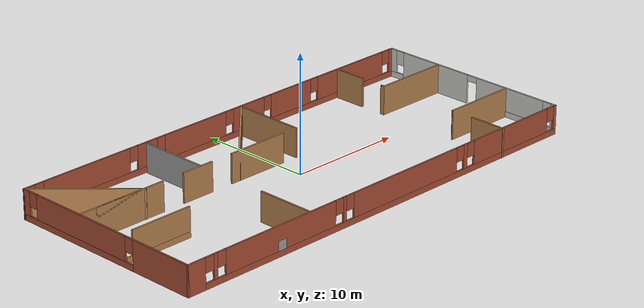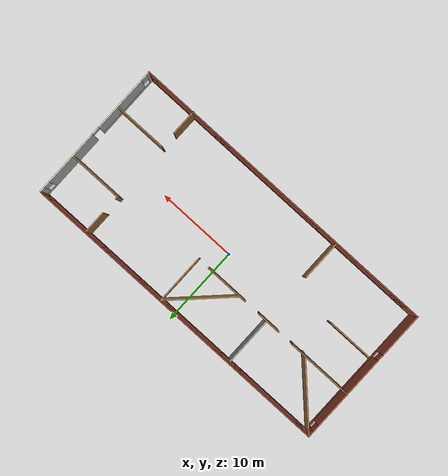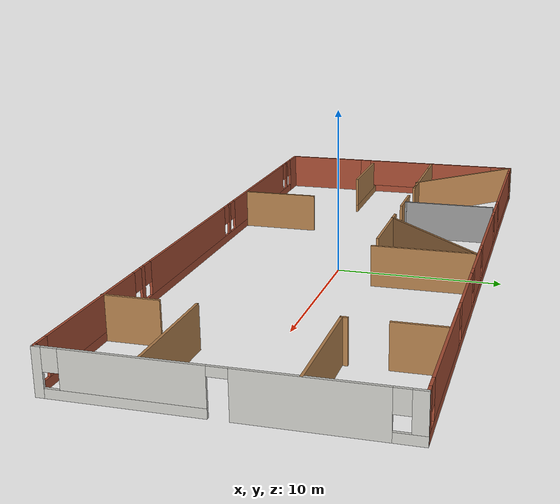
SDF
<?xml version='1.0'?>
<sdf version='1.6'>
  <model name='mybuilding'>
    <link name='Wall_28'>
      <pose frame=''>0.015532 -8.79244 0 0 -0 0</pose>
      <self_collide>0</self_collide>
      <kinematic>0</kinematic>
      <visual name='Wall_28_Visual_0'>
        <pose frame=''>-19.0594 0 1.25 0 -0 0</pose>
        <geometry>
          <box>
            <size>1.65971 0.15 2.5</size>
          </box>
        </geometry>
        <material>
          <script>
            <uri>file://media/materials/scripts/gazebo.material</uri>
            <name>Gazebo/Bricks</name>
          </script>
          <ambient>1 1 1 1</ambient>
          <shader type='pixel'/>
          <diffuse>1 1 1 1</diffuse>
          <specular>0.2 0.2 0.2 1</specular>
          <emissive>0 0 0 1</emissive>
        </material>
        <meta>
          <layer>0</layer>
        </meta>
        <transparency>0</transparency>
        <cast_shadows>1</cast_shadows>
      </visual>
      <visual name='Wall_28_Visual_1'>
        <pose frame=''>0.829853 0 0.25 0 -0 0</pose>
        <geometry>
          <box>
            <size>38.1188 0.15 0.5</size>
          </box>
        </geometry>
        <material>
          <script>
            <uri>file://media/materials/scripts/gazebo.material</uri>
            <name>Gazebo/Bricks</name>
          </script>
          <ambient>1 1 1 1</ambient>
          <shader type='pixel'/>
          <diffuse>1 1 1 1</diffuse>
          <specular>0.2 0.2 0.2 1</specular>
          <emissive>0 0 0 1</emissive>
        </material>
        <meta>
          <layer>0</layer>
        </meta>
        <transparency>0</transparency>
        <cast_shadows>1</cast_shadows>
      </visual>
      <visual name='Wall_28_Visual_2'>
        <pose frame=''>-17.26 0 1.5 0 -0 0</pose>
        <geometry>
          <box>
            <size>0.339006 0.15 2</size>
          </box>
        </geometry>
        <material>
          <script>
            <uri>file://media/materials/scripts/gazebo.material</uri>
            <name>Gazebo/Bricks</name>
          </script>
          <ambient>1 1 1 1</ambient>
          <shader type='pixel'/>
          <diffuse>1 1 1 1</diffuse>
          <specular>0.2 0.2 0.2 1</specular>
          <emissive>0 0 0 1</emissive>
        </material>
        <meta>
          <layer>0</layer>
        </meta>
        <transparency>0</transparency>
        <cast_shadows>1</cast_shadows>
      </visual>
      <visual name='Wall_28_Visual_3'>
        <pose frame=''>-10.8105 0 1.5 0 -0 0</pose>
        <geometry>
          <box>
            <size>10.96 0.15 2</size>
          </box>
        </geometry>
        <material>
          <script>
            <uri>file://media/materials/scripts/gazebo.material</uri>
            <name>Gazebo/Bricks</name>
          </script>
          <ambient>1 1 1 1</ambient>
          <shader type='pixel'/>
          <diffuse>1 1 1 1</diffuse>
          <specular>0.2 0.2 0.2 1</specular>
          <emissive>0 0 0 1</emissive>
        </material>
        <meta>
          <layer>0</layer>
        </meta>
        <transparency>0</transparency>
        <cast_shadows>1</cast_shadows>
      </visual>
      <visual name='Wall_28_Visual_4'>
        <pose frame=''>-4.37053 0 1.5 0 -0 0</pose>
        <geometry>
          <box>
            <size>0.32 0.15 2</size>
          </box>
        </geometry>
        <material>
          <script>
            <uri>file://media/materials/scripts/gazebo.material</uri>
            <name>Gazebo/Bricks</name>
          </script>
          <ambient>1 1 1 1</ambient>
          <shader type='pixel'/>
          <diffuse>1 1 1 1</diffuse>
          <specular>0.2 0.2 0.2 1</specular>
          <emissive>0 0 0 1</emissive>
        </material>
        <meta>
          <layer>0</layer>
        </meta>
        <transparency>0</transparency>
        <cast_shadows>1</cast_shadows>
      </visual>
      <visual name='Wall_28_Visual_5'>
        <pose frame=''>2.26947 0 1.5 0 -0 0</pose>
        <geometry>
          <box>
            <size>11.36 0.15 2</size>
          </box>
        </geometry>
        <material>
          <script>
            <uri>file://media/materials/scripts/gazebo.material</uri>
            <name>Gazebo/Bricks</name>
          </script>
          <ambient>1 1 1 1</ambient>
          <shader type='pixel'/>
          <diffuse>1 1 1 1</diffuse>
          <specular>0.2 0.2 0.2 1</specular>
          <emissive>0 0 0 1</emissive>
        </material>
        <meta>
          <layer>0</layer>
        </meta>
        <transparency>0</transparency>
        <cast_shadows>1</cast_shadows>
      </visual>
      <visual name='Wall_28_Visual_6'>
        <pose frame=''>8.94947 0 1.5 0 -0 0</pose>
        <geometry>
          <box>
            <size>0.4 0.15 2</size>
          </box>
        </geometry>
        <material>
          <script>
            <uri>file://media/materials/scripts/gazebo.material</uri>
            <name>Gazebo/Bricks</name>
          </script>
          <ambient>1 1 1 1</ambient>
          <shader type='pixel'/>
          <diffuse>1 1 1 1</diffuse>
          <specular>0.2 0.2 0.2 1</specular>
          <emissive>0 0 0 1</emissive>
        </material>
        <meta>
          <layer>0</layer>
        </meta>
        <transparency>0</transparency>
        <cast_shadows>1</cast_shadows>
      </visual>
      <visual name='Wall_28_Visual_7'>
        <pose frame=''>14.3495 0 1.5 0 -0 0</pose>
        <geometry>
          <box>
            <size>8.8 0.15 2</size>
          </box>
        </geometry>
        <material>
          <script>
            <uri>file://media/materials/scripts/gazebo.material</uri>
            <name>Gazebo/Bricks</name>
          </script>
          <ambient>1 1 1 1</ambient>
          <shader type='pixel'/>
          <diffuse>1 1 1 1</diffuse>
          <specular>0.2 0.2 0.2 1</specular>
          <emissive>0 0 0 1</emissive>
        </material>
        <meta>
          <layer>0</layer>
        </meta>
        <transparency>0</transparency>
        <cast_shadows>1</cast_shadows>
      </visual>
      <visual name='Wall_28_Visual_8'>
        <pose frame=''>19.7194 0 1.5 0 -0 0</pose>
        <geometry>
          <box>
            <size>0.339765 0.15 2</size>
          </box>
        </geometry>
        <material>
          <script>
            <uri>file://media/materials/scripts/gazebo.material</uri>
            <name>Gazebo/Bricks</name>
          </script>
          <ambient>1 1 1 1</ambient>
          <shader type='pixel'/>
          <diffuse>1 1 1 1</diffuse>
          <specular>0.2 0.2 0.2 1</specular>
          <emissive>0 0 0 1</emissive>
        </material>
        <meta>
          <layer>0</layer>
        </meta>
        <transparency>0</transparency>
        <cast_shadows>1</cast_shadows>
      </visual>
      <visual name='Wall_28_Visual_9'>
        <pose frame=''>-17.8295 0 1.9 0 -0 0</pose>
        <geometry>
          <box>
            <size>0.8 0.15 1.2</size>
          </box>
        </geometry>
        <material>
          <script>
            <uri>file://media/materials/scripts/gazebo.material</uri>
            <name>Gazebo/Bricks</name>
          </script>
          <ambient>1 1 1 1</ambient>
          <shader type='pixel'/>
          <diffuse>1 1 1 1</diffuse>
          <specular>0.2 0.2 0.2 1</specular>
          <emissive>0 0 0 1</emissive>
        </material>
        <meta>
          <layer>0</layer>
        </meta>
        <transparency>0</transparency>
        <cast_shadows>1</cast_shadows>
      </visual>
      <visual name='Wall_28_Visual_10'>
        <pose frame=''>-16.6905 0 1.9 0 -0 0</pose>
        <geometry>
          <box>
            <size>0.8 0.15 1.2</size>
          </box>
        </geometry>
        <material>
          <script>
            <uri>file://media/materials/scripts/gazebo.material</uri>
            <name>Gazebo/Bricks</name>
          </script>
          <ambient>1 1 1 1</ambient>
          <shader type='pixel'/>
          <diffuse>1 1 1 1</diffuse>
          <specular>0.2 0.2 0.2 1</specular>
          <emissive>0 0 0 1</emissive>
        </material>
        <meta>
          <layer>0</layer>
        </meta>
        <transparency>0</transparency>
        <cast_shadows>1</cast_shadows>
      </visual>
      <visual name='Wall_28_Visual_11'>
        <pose frame=''>-4.93053 0 1.9 0 -0 0</pose>
        <geometry>
          <box>
            <size>0.8 0.15 1.2</size>
          </box>
        </geometry>
        <material>
          <script>
            <uri>file://media/materials/scripts/gazebo.material</uri>
            <name>Gazebo/Bricks</name>
          </script>
          <ambient>1 1 1 1</ambient>
          <shader type='pixel'/>
          <diffuse>1 1 1 1</diffuse>
          <specular>0.2 0.2 0.2 1</specular>
          <emissive>0 0 0 1</emissive>
        </material>
        <meta>
          <layer>0</layer>
        </meta>
        <transparency>0</transparency>
        <cast_shadows>1</cast_shadows>
      </visual>
      <visual name='Wall_28_Visual_12'>
        <pose frame=''>-3.81053 0 1.9 0 -0 0</pose>
        <geometry>
          <box>
            <size>0.8 0.15 1.2</size>
          </box>
        </geometry>
        <material>
          <script>
            <uri>file://media/materials/scripts/gazebo.material</uri>
            <name>Gazebo/Bricks</name>
          </script>
          <ambient>1 1 1 1</ambient>
          <shader type='pixel'/>
          <diffuse>1 1 1 1</diffuse>
          <specular>0.2 0.2 0.2 1</specular>
          <emissive>0 0 0 1</emissive>
        </material>
        <meta>
          <layer>0</layer>
        </meta>
        <transparency>0</transparency>
        <cast_shadows>1</cast_shadows>
      </visual>
      <visual name='Wall_28_Visual_13'>
        <pose frame=''>8.34947 0 1.9 0 -0 0</pose>
        <geometry>
          <box>
            <size>0.8 0.15 1.2</size>
          </box>
        </geometry>
        <material>
          <script>
            <uri>file://media/materials/scripts/gazebo.material</uri>
            <name>Gazebo/Bricks</name>
          </script>
          <ambient>1 1 1 1</ambient>
          <shader type='pixel'/>
          <diffuse>1 1 1 1</diffuse>
          <specular>0.2 0.2 0.2 1</specular>
          <emissive>0 0 0 1</emissive>
        </material>
        <meta>
          <layer>0</layer>
        </meta>
        <transparency>0</transparency>
        <cast_shadows>1</cast_shadows>
      </visual>
      <visual name='Wall_28_Visual_14'>
        <pose frame=''>9.54947 0 1.9 0 -0 0</pose>
        <geometry>
          <box>
            <size>0.8 0.15 1.2</size>
          </box>
        </geometry>
        <material>
          <script>
            <uri>file://media/materials/scripts/gazebo.material</uri>
            <name>Gazebo/Bricks</name>
          </script>
          <ambient>1 1 1 1</ambient>
          <shader type='pixel'/>
          <diffuse>1 1 1 1</diffuse>
          <specular>0.2 0.2 0.2 1</specular>
          <emissive>0 0 0 1</emissive>
        </material>
        <meta>
          <layer>0</layer>
        </meta>
        <transparency>0</transparency>
        <cast_shadows>1</cast_shadows>
      </visual>
      <visual name='Wall_28_Visual_15'>
        <pose frame=''>19.1495 0 1.9 0 -0 0</pose>
        <geometry>
          <box>
            <size>0.8 0.15 1.2</size>
          </box>
        </geometry>
        <material>
          <script>
            <uri>file://media/materials/scripts/gazebo.material</uri>
            <name>Gazebo/Bricks</name>
          </script>
          <ambient>1 1 1 1</ambient>
          <shader type='pixel'/>
          <diffuse>1 1 1 1</diffuse>
          <specular>0.2 0.2 0.2 1</specular>
          <emissive>0 0 0 1</emissive>
        </material>
        <meta>
          <layer>0</layer>
        </meta>
        <transparency>0</transparency>
        <cast_shadows>1</cast_shadows>
      </visual>
      <collision name='Wall_28_Collision_0'>
        <laser_retro>0</laser_retro>
        <max_contacts>10</max_contacts>
        <pose frame=''>-19.0594 0 1.25 0 -0 0</pose>
        <geometry>
          <box>
            <size>1.65971 0.15 2.5</size>
          </box>
        </geometry>
        <surface>
          <friction>
            <ode>
              <mu>1</mu>
              <mu2>1</mu2>
              <fdir1>0 0 0</fdir1>
              <slip1>0</slip1>
              <slip2>0</slip2>
            </ode>
            <torsional>
              <coefficient>1</coefficient>
              <patch_radius>0</patch_radius>
              <surface_radius>0</surface_radius>
              <use_patch_radius>1</use_patch_radius>
              <ode>
                <slip>0</slip>
              </ode>
            </torsional>
          </friction>
          <bounce>
            <restitution_coefficient>0</restitution_coefficient>
            <threshold>1e+06</threshold>
          </bounce>
          <contact>
            <collide_without_contact>0</collide_without_contact>
            <collide_without_contact_bitmask>1</collide_without_contact_bitmask>
            <collide_bitmask>1</collide_bitmask>
            <ode>
              <soft_cfm>0</soft_cfm>
              <soft_erp>0.2</soft_erp>
              <kp>1e+13</kp>
              <kd>1</kd>
              <max_vel>0.01</max_vel>
              <min_depth>0</min_depth>
            </ode>
            <bullet>
              <split_impulse>1</split_impulse>
              <split_impulse_penetration_threshold>-0.01</split_impulse_penetration_threshold>
              <soft_cfm>0</soft_cfm>
              <soft_erp>0.2</soft_erp>
              <kp>1e+13</kp>
              <kd>1</kd>
            </bullet>
          </contact>
        </surface>
      </collision>
      <collision name='Wall_28_Collision_1'>
        <laser_retro>0</laser_retro>
        <max_contacts>10</max_contacts>
        <pose frame=''>0.829853 0 0.25 0 -0 0</pose>
        <geometry>
          <box>
            <size>38.1188 0.15 0.5</size>
          </box>
        </geometry>
        <surface>
          <friction>
            <ode>
              <mu>1</mu>
              <mu2>1</mu2>
              <fdir1>0 0 0</fdir1>
              <slip1>0</slip1>
              <slip2>0</slip2>
            </ode>
            <torsional>
              <coefficient>1</coefficient>
              <patch_radius>0</patch_radius>
              <surface_radius>0</surface_radius>
              <use_patch_radius>1</use_patch_radius>
              <ode>
                <slip>0</slip>
              </ode>
            </torsional>
          </friction>
          <bounce>
            <restitution_coefficient>0</restitution_coefficient>
            <threshold>1e+06</threshold>
          </bounce>
          <contact>
            <collide_without_contact>0</collide_without_contact>
            <collide_without_contact_bitmask>1</collide_without_contact_bitmask>
            <collide_bitmask>1</collide_bitmask>
            <ode>
              <soft_cfm>0</soft_cfm>
              <soft_erp>0.2</soft_erp>
              <kp>1e+13</kp>
              <kd>1</kd>
              <max_vel>0.01</max_vel>
              <min_depth>0</min_depth>
            </ode>
            <bullet>
              <split_impulse>1</split_impulse>
              <split_impulse_penetration_threshold>-0.01</split_impulse_penetration_threshold>
              <soft_cfm>0</soft_cfm>
              <soft_erp>0.2</soft_erp>
              <kp>1e+13</kp>
              <kd>1</kd>
            </bullet>
          </contact>
        </surface>
      </collision>
      <collision name='Wall_28_Collision_2'>
        <laser_retro>0</laser_retro>
        <max_contacts>10</max_contacts>
        <pose frame=''>-17.26 0 1.5 0 -0 0</pose>
        <geometry>
          <box>
            <size>0.339006 0.15 2</size>
          </box>
        </geometry>
        <surface>
          <friction>
            <ode>
              <mu>1</mu>
              <mu2>1</mu2>
              <fdir1>0 0 0</fdir1>
              <slip1>0</slip1>
              <slip2>0</slip2>
            </ode>
            <torsional>
              <coefficient>1</coefficient>
              <patch_radius>0</patch_radius>
              <surface_radius>0</surface_radius>
              <use_patch_radius>1</use_patch_radius>
              <ode>
                <slip>0</slip>
              </ode>
            </torsional>
          </friction>
          <bounce>
            <restitution_coefficient>0</restitution_coefficient>
            <threshold>1e+06</threshold>
          </bounce>
          <contact>
            <collide_without_contact>0</collide_without_contact>
            <collide_without_contact_bitmask>1</collide_without_contact_bitmask>
            <collide_bitmask>1</collide_bitmask>
            <ode>
              <soft_cfm>0</soft_cfm>
              <soft_erp>0.2</soft_erp>
              <kp>1e+13</kp>
              <kd>1</kd>
              <max_vel>0.01</max_vel>
              <min_depth>0</min_depth>
            </ode>
            <bullet>
              <split_impulse>1</split_impulse>
              <split_impulse_penetration_threshold>-0.01</split_impulse_penetration_threshold>
              <soft_cfm>0</soft_cfm>
              <soft_erp>0.2</soft_erp>
              <kp>1e+13</kp>
              <kd>1</kd>
            </bullet>
          </contact>
        </surface>
      </collision>
      <collision name='Wall_28_Collision_3'>
        <laser_retro>0</laser_retro>
        <max_contacts>10</max_contacts>
        <pose frame=''>-10.8105 0 1.5 0 -0 0</pose>
        <geometry>
          <box>
            <size>10.96 0.15 2</size>
          </box>
        </geometry>
        <surface>
          <friction>
            <ode>
              <mu>1</mu>
              <mu2>1</mu2>
              <fdir1>0 0 0</fdir1>
              <slip1>0</slip1>
              <slip2>0</slip2>
            </ode>
            <torsional>
              <coefficient>1</coefficient>
              <patch_radius>0</patch_radius>
              <surface_radius>0</surface_radius>
              <use_patch_radius>1</use_patch_radius>
              <ode>
                <slip>0</slip>
              </ode>
            </torsional>
          </friction>
          <bounce>
            <restitution_coefficient>0</restitution_coefficient>
            <threshold>1e+06</threshold>
          </bounce>
          <contact>
            <collide_without_contact>0</collide_without_contact>
            <collide_without_contact_bitmask>1</collide_without_contact_bitmask>
            <collide_bitmask>1</collide_bitmask>
            <ode>
              <soft_cfm>0</soft_cfm>
              <soft_erp>0.2</soft_erp>
              <kp>1e+13</kp>
              <kd>1</kd>
              <max_vel>0.01</max_vel>
              <min_depth>0</min_depth>
            </ode>
            <bullet>
              <split_impulse>1</split_impulse>
              <split_impulse_penetration_threshold>-0.01</split_impulse_penetration_threshold>
              <soft_cfm>0</soft_cfm>
              <soft_erp>0.2</soft_erp>
              <kp>1e+13</kp>
              <kd>1</kd>
            </bullet>
          </contact>
        </surface>
      </collision>
      <collision name='Wall_28_Collision_4'>
        <laser_retro>0</laser_retro>
        <max_contacts>10</max_contacts>
        <pose frame=''>-4.37053 0 1.5 0 -0 0</pose>
        <geometry>
          <box>
            <size>0.32 0.15 2</size>
          </box>
        </geometry>
        <surface>
          <friction>
            <ode>
              <mu>1</mu>
              <mu2>1</mu2>
              <fdir1>0 0 0</fdir1>
              <slip1>0</slip1>
              <slip2>0</slip2>
            </ode>
            <torsional>
              <coefficient>1</coefficient>
              <patch_radius>0</patch_radius>
              <surface_radius>0</surface_radius>
              <use_patch_radius>1</use_patch_radius>
              <ode>
                <slip>0</slip>
              </ode>
            </torsional>
          </friction>
          <bounce>
            <restitution_coefficient>0</restitution_coefficient>
            <threshold>1e+06</threshold>
          </bounce>
          <contact>
            <collide_without_contact>0</collide_without_contact>
            <collide_without_contact_bitmask>1</collide_without_contact_bitmask>
            <collide_bitmask>1</collide_bitmask>
            <ode>
              <soft_cfm>0</soft_cfm>
              <soft_erp>0.2</soft_erp>
              <kp>1e+13</kp>
              <kd>1</kd>
              <max_vel>0.01</max_vel>
              <min_depth>0</min_depth>
            </ode>
            <bullet>
              <split_impulse>1</split_impulse>
              <split_impulse_penetration_threshold>-0.01</split_impulse_penetration_threshold>
              <soft_cfm>0</soft_cfm>
              <soft_erp>0.2</soft_erp>
              <kp>1e+13</kp>
              <kd>1</kd>
            </bullet>
          </contact>
        </surface>
      </collision>
      <collision name='Wall_28_Collision_5'>
        <laser_retro>0</laser_retro>
        <max_contacts>10</max_contacts>
        <pose frame=''>2.26947 0 1.5 0 -0 0</pose>
        <geometry>
          <box>
            <size>11.36 0.15 2</size>
          </box>
        </geometry>
        <surface>
          <friction>
            <ode>
              <mu>1</mu>
              <mu2>1</mu2>
              <fdir1>0 0 0</fdir1>
              <slip1>0</slip1>
              <slip2>0</slip2>
            </ode>
            <torsional>
              <coefficient>1</coefficient>
              <patch_radius>0</patch_radius>
              <surface_radius>0</surface_radius>
              <use_patch_radius>1</use_patch_radius>
              <ode>
                <slip>0</slip>
              </ode>
            </torsional>
          </friction>
          <bounce>
            <restitution_coefficient>0</restitution_coefficient>
            <threshold>1e+06</threshold>
          </bounce>
          <contact>
            <collide_without_contact>0</collide_without_contact>
            <collide_without_contact_bitmask>1</collide_without_contact_bitmask>
            <collide_bitmask>1</collide_bitmask>
            <ode>
              <soft_cfm>0</soft_cfm>
              <soft_erp>0.2</soft_erp>
              <kp>1e+13</kp>
              <kd>1</kd>
              <max_vel>0.01</max_vel>
              <min_depth>0</min_depth>
            </ode>
            <bullet>
              <split_impulse>1</split_impulse>
              <split_impulse_penetration_threshold>-0.01</split_impulse_penetration_threshold>
              <soft_cfm>0</soft_cfm>
              <soft_erp>0.2</soft_erp>
              <kp>1e+13</kp>
              <kd>1</kd>
            </bullet>
          </contact>
        </surface>
      </collision>
      <collision name='Wall_28_Collision_6'>
        <laser_retro>0</laser_retro>
        <max_contacts>10</max_contacts>
        <pose frame=''>8.94947 0 1.5 0 -0 0</pose>
        <geometry>
          <box>
            <size>0.4 0.15 2</size>
          </box>
        </geometry>
        <surface>
          <friction>
            <ode>
              <mu>1</mu>
              <mu2>1</mu2>
              <fdir1>0 0 0</fdir1>
              <slip1>0</slip1>
              <slip2>0</slip2>
            </ode>
            <torsional>
              <coefficient>1</coefficient>
              <patch_radius>0</patch_radius>
              <surface_radius>0</surface_radius>
              <use_patch_radius>1</use_patch_radius>
              <ode>
                <slip>0</slip>
              </ode>
            </torsional>
          </friction>
          <bounce>
            <restitution_coefficient>0</restitution_coefficient>
            <threshold>1e+06</threshold>
          </bounce>
          <contact>
            <collide_without_contact>0</collide_without_contact>
            <collide_without_contact_bitmask>1</collide_without_contact_bitmask>
            <collide_bitmask>1</collide_bitmask>
            <ode>
              <soft_cfm>0</soft_cfm>
              <soft_erp>0.2</soft_erp>
              <kp>1e+13</kp>
              <kd>1</kd>
              <max_vel>0.01</max_vel>
              <min_depth>0</min_depth>
            </ode>
            <bullet>
              <split_impulse>1</split_impulse>
              <split_impulse_penetration_threshold>-0.01</split_impulse_penetration_threshold>
              <soft_cfm>0</soft_cfm>
              <soft_erp>0.2</soft_erp>
              <kp>1e+13</kp>
              <kd>1</kd>
            </bullet>
          </contact>
        </surface>
      </collision>
      <collision name='Wall_28_Collision_7'>
        <laser_retro>0</laser_retro>
        <max_contacts>10</max_contacts>
        <pose frame=''>14.3495 0 1.5 0 -0 0</pose>
        <geometry>
          <box>
            <size>8.8 0.15 2</size>
          </box>
        </geometry>
        <surface>
          <friction>
            <ode>
              <mu>1</mu>
              <mu2>1</mu2>
              <fdir1>0 0 0</fdir1>
              <slip1>0</slip1>
              <slip2>0</slip2>
            </ode>
            <torsional>
              <coefficient>1</coefficient>
              <patch_radius>0</patch_radius>
              <surface_radius>0</surface_radius>
              <use_patch_radius>1</use_patch_radius>
              <ode>
                <slip>0</slip>
              </ode>
            </torsional>
          </friction>
          <bounce>
            <restitution_coefficient>0</restitution_coefficient>
            <threshold>1e+06</threshold>
          </bounce>
          <contact>
            <collide_without_contact>0</collide_without_contact>
            <collide_without_contact_bitmask>1</collide_without_contact_bitmask>
            <collide_bitmask>1</collide_bitmask>
            <ode>
              <soft_cfm>0</soft_cfm>
              <soft_erp>0.2</soft_erp>
              <kp>1e+13</kp>
              <kd>1</kd>
              <max_vel>0.01</max_vel>
              <min_depth>0</min_depth>
            </ode>
            <bullet>
              <split_impulse>1</split_impulse>
              <split_impulse_penetration_threshold>-0.01</split_impulse_penetration_threshold>
              <soft_cfm>0</soft_cfm>
              <soft_erp>0.2</soft_erp>
              <kp>1e+13</kp>
              <kd>1</kd>
            </bullet>
          </contact>
        </surface>
      </collision>
      <collision name='Wall_28_Collision_8'>
        <laser_retro>0</laser_retro>
        <max_contacts>10</max_contacts>
        <pose frame=''>19.7194 0 1.5 0 -0 0</pose>
        <geometry>
          <box>
            <size>0.339765 0.15 2</size>
          </box>
        </geometry>
        <surface>
          <friction>
            <ode>
              <mu>1</mu>
              <mu2>1</mu2>
              <fdir1>0 0 0</fdir1>
              <slip1>0</slip1>
              <slip2>0</slip2>
            </ode>
            <torsional>
              <coefficient>1</coefficient>
              <patch_radius>0</patch_radius>
              <surface_radius>0</surface_radius>
              <use_patch_radius>1</use_patch_radius>
              <ode>
                <slip>0</slip>
              </ode>
            </torsional>
          </friction>
          <bounce>
            <restitution_coefficient>0</restitution_coefficient>
            <threshold>1e+06</threshold>
          </bounce>
          <contact>
            <collide_without_contact>0</collide_without_contact>
            <collide_without_contact_bitmask>1</collide_without_contact_bitmask>
            <collide_bitmask>1</collide_bitmask>
            <ode>
              <soft_cfm>0</soft_cfm>
              <soft_erp>0.2</soft_erp>
              <kp>1e+13</kp>
              <kd>1</kd>
              <max_vel>0.01</max_vel>
              <min_depth>0</min_depth>
            </ode>
            <bullet>
              <split_impulse>1</split_impulse>
              <split_impulse_penetration_threshold>-0.01</split_impulse_penetration_threshold>
              <soft_cfm>0</soft_cfm>
              <soft_erp>0.2</soft_erp>
              <kp>1e+13</kp>
              <kd>1</kd>
            </bullet>
          </contact>
        </surface>
      </collision>
      <collision name='Wall_28_Collision_9'>
        <laser_retro>0</laser_retro>
        <max_contacts>10</max_contacts>
        <pose frame=''>-17.8295 0 1.9 0 -0 0</pose>
        <geometry>
          <box>
            <size>0.8 0.15 1.2</size>
          </box>
        </geometry>
        <surface>
          <friction>
            <ode>
              <mu>1</mu>
              <mu2>1</mu2>
              <fdir1>0 0 0</fdir1>
              <slip1>0</slip1>
              <slip2>0</slip2>
            </ode>
            <torsional>
              <coefficient>1</coefficient>
              <patch_radius>0</patch_radius>
              <surface_radius>0</surface_radius>
              <use_patch_radius>1</use_patch_radius>
              <ode>
                <slip>0</slip>
              </ode>
            </torsional>
          </friction>
          <bounce>
            <restitution_coefficient>0</restitution_coefficient>
            <threshold>1e+06</threshold>
          </bounce>
          <contact>
            <collide_without_contact>0</collide_without_contact>
            <collide_without_contact_bitmask>1</collide_without_contact_bitmask>
            <collide_bitmask>1</collide_bitmask>
            <ode>
              <soft_cfm>0</soft_cfm>
              <soft_erp>0.2</soft_erp>
              <kp>1e+13</kp>
              <kd>1</kd>
              <max_vel>0.01</max_vel>
              <min_depth>0</min_depth>
            </ode>
            <bullet>
              <split_impulse>1</split_impulse>
              <split_impulse_penetration_threshold>-0.01</split_impulse_penetration_threshold>
              <soft_cfm>0</soft_cfm>
              <soft_erp>0.2</soft_erp>
              <kp>1e+13</kp>
              <kd>1</kd>
            </bullet>
          </contact>
        </surface>
      </collision>
      <collision name='Wall_28_Collision_11'>
        <laser_retro>0</laser_retro>
        <max_contacts>10</max_contacts>
        <pose frame=''>-4.93053 0 1.9 0 -0 0</pose>
        <geometry>
          <box>
            <size>0.8 0.15 1.2</size>
          </box>
        </geometry>
        <surface>
          <friction>
            <ode>
              <mu>1</mu>
              <mu2>1</mu2>
              <fdir1>0 0 0</fdir1>
              <slip1>0</slip1>
              <slip2>0</slip2>
            </ode>
            <torsional>
              <coefficient>1</coefficient>
              <patch_radius>0</patch_radius>
              <surface_radius>0</surface_radius>
              <use_patch_radius>1</use_patch_radius>
              <ode>
                <slip>0</slip>
              </ode>
            </torsional>
          </friction>
          <bounce>
            <restitution_coefficient>0</restitution_coefficient>
            <threshold>1e+06</threshold>
          </bounce>
          <contact>
            <collide_without_contact>0</collide_without_contact>
            <collide_without_contact_bitmask>1</collide_without_contact_bitmask>
            <collide_bitmask>1</collide_bitmask>
            <ode>
              <soft_cfm>0</soft_cfm>
              <soft_erp>0.2</soft_erp>
              <kp>1e+13</kp>
              <kd>1</kd>
              <max_vel>0.01</max_vel>
              <min_depth>0</min_depth>
            </ode>
            <bullet>
              <split_impulse>1</split_impulse>
              <split_impulse_penetration_threshold>-0.01</split_impulse_penetration_threshold>
              <soft_cfm>0</soft_cfm>
              <soft_erp>0.2</soft_erp>
              <kp>1e+13</kp>
              <kd>1</kd>
            </bullet>
          </contact>
        </surface>
      </collision>
      <collision name='Wall_28_Collision_10'>
        <laser_retro>0</laser_retro>
        <max_contacts>10</max_contacts>
        <pose frame=''>-16.6905 0 1.9 0 -0 0</pose>
        <geometry>
          <box>
            <size>0.8 0.15 1.2</size>
          </box>
        </geometry>
        <surface>
          <friction>
            <ode>
              <mu>1</mu>
              <mu2>1</mu2>
              <fdir1>0 0 0</fdir1>
              <slip1>0</slip1>
              <slip2>0</slip2>
            </ode>
            <torsional>
              <coefficient>1</coefficient>
              <patch_radius>0</patch_radius>
              <surface_radius>0</surface_radius>
              <use_patch_radius>1</use_patch_radius>
              <ode>
                <slip>0</slip>
              </ode>
            </torsional>
          </friction>
          <bounce>
            <restitution_coefficient>0</restitution_coefficient>
            <threshold>1e+06</threshold>
          </bounce>
          <contact>
            <collide_without_contact>0</collide_without_contact>
            <collide_without_contact_bitmask>1</collide_without_contact_bitmask>
            <collide_bitmask>1</collide_bitmask>
            <ode>
              <soft_cfm>0</soft_cfm>
              <soft_erp>0.2</soft_erp>
              <kp>1e+13</kp>
              <kd>1</kd>
              <max_vel>0.01</max_vel>
              <min_depth>0</min_depth>
            </ode>
            <bullet>
              <split_impulse>1</split_impulse>
              <split_impulse_penetration_threshold>-0.01</split_impulse_penetration_threshold>
              <soft_cfm>0</soft_cfm>
              <soft_erp>0.2</soft_erp>
              <kp>1e+13</kp>
              <kd>1</kd>
            </bullet>
          </contact>
        </surface>
      </collision>
      <collision name='Wall_28_Collision_12'>
        <laser_retro>0</laser_retro>
        <max_contacts>10</max_contacts>
        <pose frame=''>-3.81053 0 1.9 0 -0 0</pose>
        <geometry>
          <box>
            <size>0.8 0.15 1.2</size>
          </box>
        </geometry>
        <surface>
          <friction>
            <ode>
              <mu>1</mu>
              <mu2>1</mu2>
              <fdir1>0 0 0</fdir1>
              <slip1>0</slip1>
              <slip2>0</slip2>
            </ode>
            <torsional>
              <coefficient>1</coefficient>
              <patch_radius>0</patch_radius>
              <surface_radius>0</surface_radius>
              <use_patch_radius>1</use_patch_radius>
              <ode>
                <slip>0</slip>
              </ode>
            </torsional>
          </friction>
          <bounce>
            <restitution_coefficient>0</restitution_coefficient>
            <threshold>1e+06</threshold>
          </bounce>
          <contact>
            <collide_without_contact>0</collide_without_contact>
            <collide_without_contact_bitmask>1</collide_without_contact_bitmask>
            <collide_bitmask>1</collide_bitmask>
            <ode>
              <soft_cfm>0</soft_cfm>
              <soft_erp>0.2</soft_erp>
              <kp>1e+13</kp>
              <kd>1</kd>
              <max_vel>0.01</max_vel>
              <min_depth>0</min_depth>
            </ode>
            <bullet>
              <split_impulse>1</split_impulse>
              <split_impulse_penetration_threshold>-0.01</split_impulse_penetration_threshold>
              <soft_cfm>0</soft_cfm>
              <soft_erp>0.2</soft_erp>
              <kp>1e+13</kp>
              <kd>1</kd>
            </bullet>
          </contact>
        </surface>
      </collision>
      <collision name='Wall_28_Collision_14'>
        <laser_retro>0</laser_retro>
        <max_contacts>10</max_contacts>
        <pose frame=''>9.54947 0 1.9 0 -0 0</pose>
        <geometry>
          <box>
            <size>0.8 0.15 1.2</size>
          </box>
        </geometry>
        <surface>
          <friction>
            <ode>
              <mu>1</mu>
              <mu2>1</mu2>
              <fdir1>0 0 0</fdir1>
              <slip1>0</slip1>
              <slip2>0</slip2>
            </ode>
            <torsional>
              <coefficient>1</coefficient>
              <patch_radius>0</patch_radius>
              <surface_radius>0</surface_radius>
              <use_patch_radius>1</use_patch_radius>
              <ode>
                <slip>0</slip>
              </ode>
            </torsional>
          </friction>
          <bounce>
            <restitution_coefficient>0</restitution_coefficient>
            <threshold>1e+06</threshold>
          </bounce>
          <contact>
            <collide_without_contact>0</collide_without_contact>
            <collide_without_contact_bitmask>1</collide_without_contact_bitmask>
            <collide_bitmask>1</collide_bitmask>
            <ode>
              <soft_cfm>0</soft_cfm>
              <soft_erp>0.2</soft_erp>
              <kp>1e+13</kp>
              <kd>1</kd>
              <max_vel>0.01</max_vel>
              <min_depth>0</min_depth>
            </ode>
            <bullet>
              <split_impulse>1</split_impulse>
              <split_impulse_penetration_threshold>-0.01</split_impulse_penetration_threshold>
              <soft_cfm>0</soft_cfm>
              <soft_erp>0.2</soft_erp>
              <kp>1e+13</kp>
              <kd>1</kd>
            </bullet>
          </contact>
        </surface>
      </collision>
      <collision name='Wall_28_Collision_13'>
        <laser_retro>0</laser_retro>
        <max_contacts>10</max_contacts>
        <pose frame=''>8.34947 0 1.9 0 -0 0</pose>
        <geometry>
          <box>
            <size>0.8 0.15 1.2</size>
          </box>
        </geometry>
        <surface>
          <friction>
            <ode>
              <mu>1</mu>
              <mu2>1</mu2>
              <fdir1>0 0 0</fdir1>
              <slip1>0</slip1>
              <slip2>0</slip2>
            </ode>
            <torsional>
              <coefficient>1</coefficient>
              <patch_radius>0</patch_radius>
              <surface_radius>0</surface_radius>
              <use_patch_radius>1</use_patch_radius>
              <ode>
                <slip>0</slip>
              </ode>
            </torsional>
          </friction>
          <bounce>
            <restitution_coefficient>0</restitution_coefficient>
            <threshold>1e+06</threshold>
          </bounce>
          <contact>
            <collide_without_contact>0</collide_without_contact>
            <collide_without_contact_bitmask>1</collide_without_contact_bitmask>
            <collide_bitmask>1</collide_bitmask>
            <ode>
              <soft_cfm>0</soft_cfm>
              <soft_erp>0.2</soft_erp>
              <kp>1e+13</kp>
              <kd>1</kd>
              <max_vel>0.01</max_vel>
              <min_depth>0</min_depth>
            </ode>
            <bullet>
              <split_impulse>1</split_impulse>
              <split_impulse_penetration_threshold>-0.01</split_impulse_penetration_threshold>
              <soft_cfm>0</soft_cfm>
              <soft_erp>0.2</soft_erp>
              <kp>1e+13</kp>
              <kd>1</kd>
            </bullet>
          </contact>
        </surface>
      </collision>
      <collision name='Wall_28_Collision_15'>
        <laser_retro>0</laser_retro>
        <max_contacts>10</max_contacts>
        <pose frame=''>19.1495 0 1.9 0 -0 0</pose>
        <geometry>
          <box>
            <size>0.8 0.15 1.2</size>
          </box>
        </geometry>
        <surface>
          <friction>
            <ode>
              <mu>1</mu>
              <mu2>1</mu2>
              <fdir1>0 0 0</fdir1>
              <slip1>0</slip1>
              <slip2>0</slip2>
            </ode>
            <torsional>
              <coefficient>1</coefficient>
              <patch_radius>0</patch_radius>
              <surface_radius>0</surface_radius>
              <use_patch_radius>1</use_patch_radius>
              <ode>
                <slip>0</slip>
              </ode>
            </torsional>
          </friction>
          <bounce>
            <restitution_coefficient>0</restitution_coefficient>
            <threshold>1e+06</threshold>
          </bounce>
          <contact>
            <collide_without_contact>0</collide_without_contact>
            <collide_without_contact_bitmask>1</collide_without_contact_bitmask>
            <collide_bitmask>1</collide_bitmask>
            <ode>
              <soft_cfm>0</soft_cfm>
              <soft_erp>0.2</soft_erp>
              <kp>1e+13</kp>
              <kd>1</kd>
              <max_vel>0.01</max_vel>
              <min_depth>0</min_depth>
            </ode>
            <bullet>
              <split_impulse>1</split_impulse>
              <split_impulse_penetration_threshold>-0.01</split_impulse_penetration_threshold>
              <soft_cfm>0</soft_cfm>
              <soft_erp>0.2</soft_erp>
              <kp>1e+13</kp>
              <kd>1</kd>
            </bullet>
          </contact>
        </surface>
      </collision>
    </link>
    <link name='Wall_41'>
      <pose frame=''>19.8298 0.007562 0 0 -0 1.5708</pose>
      <self_collide>0</self_collide>
      <kinematic>0</kinematic>
      <visual name='Wall_41_Visual_9'>
        <pose frame=''>-0.150712 0 2.25 0 -0 0</pose>
        <geometry>
          <box>
            <size>1 0.15 0.5</size>
          </box>
        </geometry>
        <material>
          <script>
            <uri>file://media/materials/scripts/gazebo.material</uri>
            <name>Gazebo/CeilingTiled</name>
          </script>
          <ambient>1 0.972549 0.847059 1</ambient>
          <shader type='pixel'/>
          <diffuse>1 1 1 1</diffuse>
          <specular>0 0 0 1</specular>
          <emissive>0 0 0 1</emissive>
        </material>
        <meta>
          <layer>0</layer>
        </meta>
        <transparency>0</transparency>
        <cast_shadows>1</cast_shadows>
      </visual>
      <visual name='Wall_41_Visual_0'>
        <pose frame=''>-8.63665 0 1.25 0 -0 0</pose>
        <geometry>
          <box>
            <size>0.476697 0.15 2.5</size>
          </box>
        </geometry>
        <material>
          <script>
            <uri>file://media/materials/scripts/gazebo.material</uri>
            <name>Gazebo/CeilingTiled</name>
          </script>
          <ambient>1 0.972549 0.847059 1</ambient>
          <shader type='pixel'/>
          <diffuse>1 1 1 1</diffuse>
          <specular>0 0 0 1</specular>
          <emissive>0 0 0 1</emissive>
        </material>
        <meta>
          <layer>0</layer>
        </meta>
        <transparency>0</transparency>
        <cast_shadows>1</cast_shadows>
      </visual>
      <visual name='Wall_41_Visual_1'>
        <pose frame=''>3.85638 0 1.25 0 -0 0</pose>
        <geometry>
          <box>
            <size>7.01419 0.15 2.5</size>
          </box>
        </geometry>
        <material>
          <script>
            <uri>file://media/materials/scripts/gazebo.material</uri>
            <name>Gazebo/CeilingTiled</name>
          </script>
          <ambient>1 0.972549 0.847059 1</ambient>
          <shader type='pixel'/>
          <diffuse>1 1 1 1</diffuse>
          <specular>0 0 0 1</specular>
          <emissive>0 0 0 1</emissive>
        </material>
        <meta>
          <layer>0</layer>
        </meta>
        <transparency>0</transparency>
        <cast_shadows>1</cast_shadows>
      </visual>
      <visual name='Wall_41_Visual_2'>
        <pose frame=''>-4.52451 0 0.25 0 -0 0</pose>
        <geometry>
          <box>
            <size>7.74759 0.15 0.5</size>
          </box>
        </geometry>
        <material>
          <script>
            <uri>file://media/materials/scripts/gazebo.material</uri>
            <name>Gazebo/CeilingTiled</name>
          </script>
          <ambient>1 0.972549 0.847059 1</ambient>
          <shader type='pixel'/>
          <diffuse>1 1 1 1</diffuse>
          <specular>0 0 0 1</specular>
          <emissive>0 0 0 1</emissive>
        </material>
        <meta>
          <layer>0</layer>
        </meta>
        <transparency>0</transparency>
        <cast_shadows>1</cast_shadows>
      </visual>
      <visual name='Wall_41_Visual_3'>
        <pose frame=''>8.11924 0 0.25 0 -0 0</pose>
        <geometry>
          <box>
            <size>1.51152 0.15 0.5</size>
          </box>
        </geometry>
        <material>
          <script>
            <uri>file://media/materials/scripts/gazebo.material</uri>
            <name>Gazebo/CeilingTiled</name>
          </script>
          <ambient>1 0.972549 0.847059 1</ambient>
          <shader type='pixel'/>
          <diffuse>1 1 1 1</diffuse>
          <specular>0 0 0 1</specular>
          <emissive>0 0 0 1</emissive>
        </material>
        <meta>
          <layer>0</layer>
        </meta>
        <transparency>0</transparency>
        <cast_shadows>1</cast_shadows>
      </visual>
      <visual name='Wall_41_Visual_4'>
        <pose frame=''>-4.12451 0 1.5 0 -0 0</pose>
        <geometry>
          <box>
            <size>6.94759 0.15 2</size>
          </box>
        </geometry>
        <material>
          <script>
            <uri>file://media/materials/scripts/gazebo.material</uri>
            <name>Gazebo/CeilingTiled</name>
          </script>
          <ambient>1 0.972549 0.847059 1</ambient>
          <shader type='pixel'/>
          <diffuse>1 1 1 1</diffuse>
          <specular>0 0 0 1</specular>
          <emissive>0 0 0 1</emissive>
        </material>
        <meta>
          <layer>0</layer>
        </meta>
        <transparency>0</transparency>
        <cast_shadows>1</cast_shadows>
      </visual>
      <visual name='Wall_41_Visual_5'>
        <pose frame=''>-4.12451 0 1.5 0 -0 0</pose>
        <geometry>
          <box>
            <size>6.94759 0.15 2</size>
          </box>
        </geometry>
        <material>
          <script>
            <uri>file://media/materials/scripts/gazebo.material</uri>
            <name>Gazebo/CeilingTiled</name>
          </script>
          <ambient>1 0.972549 0.847059 1</ambient>
          <shader type='pixel'/>
          <diffuse>1 1 1 1</diffuse>
          <specular>0 0 0 1</specular>
          <emissive>0 0 0 1</emissive>
        </material>
        <meta>
          <layer>0</layer>
        </meta>
        <transparency>0</transparency>
        <cast_shadows>1</cast_shadows>
      </visual>
      <visual name='Wall_41_Visual_6'>
        <pose frame=''>8.51924 0 1.5 0 -0 0</pose>
        <geometry>
          <box>
            <size>0.711521 0.15 2</size>
          </box>
        </geometry>
        <material>
          <script>
            <uri>file://media/materials/scripts/gazebo.material</uri>
            <name>Gazebo/CeilingTiled</name>
          </script>
          <ambient>1 0.972549 0.847059 1</ambient>
          <shader type='pixel'/>
          <diffuse>1 1 1 1</diffuse>
          <specular>0 0 0 1</specular>
          <emissive>0 0 0 1</emissive>
        </material>
        <meta>
          <layer>0</layer>
        </meta>
        <transparency>0</transparency>
        <cast_shadows>1</cast_shadows>
      </visual>
      <visual name='Wall_41_Visual_7'>
        <pose frame=''>-7.9983 0 1.9 0 -0 0</pose>
        <geometry>
          <box>
            <size>0.8 0.15 1.2</size>
          </box>
        </geometry>
        <material>
          <script>
            <uri>file://media/materials/scripts/gazebo.material</uri>
            <name>Gazebo/CeilingTiled</name>
          </script>
          <ambient>1 0.972549 0.847059 1</ambient>
          <shader type='pixel'/>
          <diffuse>1 1 1 1</diffuse>
          <specular>0 0 0 1</specular>
          <emissive>0 0 0 1</emissive>
        </material>
        <meta>
          <layer>0</layer>
        </meta>
        <transparency>0</transparency>
        <cast_shadows>1</cast_shadows>
      </visual>
      <visual name='Wall_41_Visual_8'>
        <pose frame=''>7.76348 0 1.9 0 -0 0</pose>
        <geometry>
          <box>
            <size>0.8 0.15 1.2</size>
          </box>
        </geometry>
        <material>
          <script>
            <uri>file://media/materials/scripts/gazebo.material</uri>
            <name>Gazebo/CeilingTiled</name>
          </script>
          <ambient>1 0.972549 0.847059 1</ambient>
          <shader type='pixel'/>
          <diffuse>1 1 1 1</diffuse>
          <specular>0 0 0 1</specular>
          <emissive>0 0 0 1</emissive>
        </material>
        <meta>
          <layer>0</layer>
        </meta>
        <transparency>0</transparency>
        <cast_shadows>1</cast_shadows>
      </visual>
      <visual name='Wall_41_Visual_10'>
        <pose frame=''>-0.150712 0 2.25 0 -0 0</pose>
        <geometry>
          <box>
            <size>1 0.15 0.5</size>
          </box>
        </geometry>
        <material>
          <script>
            <uri>file://media/materials/scripts/gazebo.material</uri>
            <name>Gazebo/CeilingTiled</name>
          </script>
          <ambient>1 0.972549 0.847059 1</ambient>
          <shader type='pixel'/>
          <diffuse>1 1 1 1</diffuse>
          <specular>0 0 0 1</specular>
          <emissive>0 0 0 1</emissive>
        </material>
        <meta>
          <layer>0</layer>
        </meta>
        <transparency>0</transparency>
        <cast_shadows>1</cast_shadows>
      </visual>
      <collision name='Wall_41_Collision_0'>
        <laser_retro>0</laser_retro>
        <max_contacts>10</max_contacts>
        <pose frame=''>-8.63665 0 1.25 0 -0 0</pose>
        <geometry>
          <box>
            <size>0.476697 0.15 2.5</size>
          </box>
        </geometry>
        <surface>
          <friction>
            <ode>
              <mu>1</mu>
              <mu2>1</mu2>
              <fdir1>0 0 0</fdir1>
              <slip1>0</slip1>
              <slip2>0</slip2>
            </ode>
            <torsional>
              <coefficient>1</coefficient>
              <patch_radius>0</patch_radius>
              <surface_radius>0</surface_radius>
              <use_patch_radius>1</use_patch_radius>
              <ode>
                <slip>0</slip>
              </ode>
            </torsional>
          </friction>
          <bounce>
            <restitution_coefficient>0</restitution_coefficient>
            <threshold>1e+06</threshold>
          </bounce>
          <contact>
            <collide_without_contact>0</collide_without_contact>
            <collide_without_contact_bitmask>1</collide_without_contact_bitmask>
            <collide_bitmask>1</collide_bitmask>
            <ode>
              <soft_cfm>0</soft_cfm>
              <soft_erp>0.2</soft_erp>
              <kp>1e+13</kp>
              <kd>1</kd>
              <max_vel>0.01</max_vel>
              <min_depth>0</min_depth>
            </ode>
            <bullet>
              <split_impulse>1</split_impulse>
              <split_impulse_penetration_threshold>-0.01</split_impulse_penetration_threshold>
              <soft_cfm>0</soft_cfm>
              <soft_erp>0.2</soft_erp>
              <kp>1e+13</kp>
              <kd>1</kd>
            </bullet>
          </contact>
        </surface>
      </collision>
      <collision name='Wall_41_Collision_1'>
        <laser_retro>0</laser_retro>
        <max_contacts>10</max_contacts>
        <pose frame=''>3.85638 0 1.25 0 -0 0</pose>
        <geometry>
          <box>
            <size>7.01419 0.15 2.5</size>
          </box>
        </geometry>
        <surface>
          <friction>
            <ode>
              <mu>1</mu>
              <mu2>1</mu2>
              <fdir1>0 0 0</fdir1>
              <slip1>0</slip1>
              <slip2>0</slip2>
            </ode>
            <torsional>
              <coefficient>1</coefficient>
              <patch_radius>0</patch_radius>
              <surface_radius>0</surface_radius>
              <use_patch_radius>1</use_patch_radius>
              <ode>
                <slip>0</slip>
              </ode>
            </torsional>
          </friction>
          <bounce>
            <restitution_coefficient>0</restitution_coefficient>
            <threshold>1e+06</threshold>
          </bounce>
          <contact>
            <collide_without_contact>0</collide_without_contact>
            <collide_without_contact_bitmask>1</collide_without_contact_bitmask>
            <collide_bitmask>1</collide_bitmask>
            <ode>
              <soft_cfm>0</soft_cfm>
              <soft_erp>0.2</soft_erp>
              <kp>1e+13</kp>
              <kd>1</kd>
              <max_vel>0.01</max_vel>
              <min_depth>0</min_depth>
            </ode>
            <bullet>
              <split_impulse>1</split_impulse>
              <split_impulse_penetration_threshold>-0.01</split_impulse_penetration_threshold>
              <soft_cfm>0</soft_cfm>
              <soft_erp>0.2</soft_erp>
              <kp>1e+13</kp>
              <kd>1</kd>
            </bullet>
          </contact>
        </surface>
      </collision>
      <collision name='Wall_41_Collision_2'>
        <laser_retro>0</laser_retro>
        <max_contacts>10</max_contacts>
        <pose frame=''>-4.52451 0 0.25 0 -0 0</pose>
        <geometry>
          <box>
            <size>7.74759 0.15 0.5</size>
          </box>
        </geometry>
        <surface>
          <friction>
            <ode>
              <mu>1</mu>
              <mu2>1</mu2>
              <fdir1>0 0 0</fdir1>
              <slip1>0</slip1>
              <slip2>0</slip2>
            </ode>
            <torsional>
              <coefficient>1</coefficient>
              <patch_radius>0</patch_radius>
              <surface_radius>0</surface_radius>
              <use_patch_radius>1</use_patch_radius>
              <ode>
                <slip>0</slip>
              </ode>
            </torsional>
          </friction>
          <bounce>
            <restitution_coefficient>0</restitution_coefficient>
            <threshold>1e+06</threshold>
          </bounce>
          <contact>
            <collide_without_contact>0</collide_without_contact>
            <collide_without_contact_bitmask>1</collide_without_contact_bitmask>
            <collide_bitmask>1</collide_bitmask>
            <ode>
              <soft_cfm>0</soft_cfm>
              <soft_erp>0.2</soft_erp>
              <kp>1e+13</kp>
              <kd>1</kd>
              <max_vel>0.01</max_vel>
              <min_depth>0</min_depth>
            </ode>
            <bullet>
              <split_impulse>1</split_impulse>
              <split_impulse_penetration_threshold>-0.01</split_impulse_penetration_threshold>
              <soft_cfm>0</soft_cfm>
              <soft_erp>0.2</soft_erp>
              <kp>1e+13</kp>
              <kd>1</kd>
            </bullet>
          </contact>
        </surface>
      </collision>
      <collision name='Wall_41_Collision_3'>
        <laser_retro>0</laser_retro>
        <max_contacts>10</max_contacts>
        <pose frame=''>8.11924 0 0.25 0 -0 0</pose>
        <geometry>
          <box>
            <size>1.51152 0.15 0.5</size>
          </box>
        </geometry>
        <surface>
          <friction>
            <ode>
              <mu>1</mu>
              <mu2>1</mu2>
              <fdir1>0 0 0</fdir1>
              <slip1>0</slip1>
              <slip2>0</slip2>
            </ode>
            <torsional>
              <coefficient>1</coefficient>
              <patch_radius>0</patch_radius>
              <surface_radius>0</surface_radius>
              <use_patch_radius>1</use_patch_radius>
              <ode>
                <slip>0</slip>
              </ode>
            </torsional>
          </friction>
          <bounce>
            <restitution_coefficient>0</restitution_coefficient>
            <threshold>1e+06</threshold>
          </bounce>
          <contact>
            <collide_without_contact>0</collide_without_contact>
            <collide_without_contact_bitmask>1</collide_without_contact_bitmask>
            <collide_bitmask>1</collide_bitmask>
            <ode>
              <soft_cfm>0</soft_cfm>
              <soft_erp>0.2</soft_erp>
              <kp>1e+13</kp>
              <kd>1</kd>
              <max_vel>0.01</max_vel>
              <min_depth>0</min_depth>
            </ode>
            <bullet>
              <split_impulse>1</split_impulse>
              <split_impulse_penetration_threshold>-0.01</split_impulse_penetration_threshold>
              <soft_cfm>0</soft_cfm>
              <soft_erp>0.2</soft_erp>
              <kp>1e+13</kp>
              <kd>1</kd>
            </bullet>
          </contact>
        </surface>
      </collision>
      <collision name='Wall_41_Collision_4'>
        <laser_retro>0</laser_retro>
        <max_contacts>10</max_contacts>
        <pose frame=''>-4.12451 0 1.5 0 -0 0</pose>
        <geometry>
          <box>
            <size>6.94759 0.15 2</size>
          </box>
        </geometry>
        <surface>
          <friction>
            <ode>
              <mu>1</mu>
              <mu2>1</mu2>
              <fdir1>0 0 0</fdir1>
              <slip1>0</slip1>
              <slip2>0</slip2>
            </ode>
            <torsional>
              <coefficient>1</coefficient>
              <patch_radius>0</patch_radius>
              <surface_radius>0</surface_radius>
              <use_patch_radius>1</use_patch_radius>
              <ode>
                <slip>0</slip>
              </ode>
            </torsional>
          </friction>
          <bounce>
            <restitution_coefficient>0</restitution_coefficient>
            <threshold>1e+06</threshold>
          </bounce>
          <contact>
            <collide_without_contact>0</collide_without_contact>
            <collide_without_contact_bitmask>1</collide_without_contact_bitmask>
            <collide_bitmask>1</collide_bitmask>
            <ode>
              <soft_cfm>0</soft_cfm>
              <soft_erp>0.2</soft_erp>
              <kp>1e+13</kp>
              <kd>1</kd>
              <max_vel>0.01</max_vel>
              <min_depth>0</min_depth>
            </ode>
            <bullet>
              <split_impulse>1</split_impulse>
              <split_impulse_penetration_threshold>-0.01</split_impulse_penetration_threshold>
              <soft_cfm>0</soft_cfm>
              <soft_erp>0.2</soft_erp>
              <kp>1e+13</kp>
              <kd>1</kd>
            </bullet>
          </contact>
        </surface>
      </collision>
      <collision name='Wall_41_Collision_5'>
        <laser_retro>0</laser_retro>
        <max_contacts>10</max_contacts>
        <pose frame=''>-4.12451 0 1.5 0 -0 0</pose>
        <geometry>
          <box>
            <size>6.94759 0.15 2</size>
          </box>
        </geometry>
        <surface>
          <friction>
            <ode>
              <mu>1</mu>
              <mu2>1</mu2>
              <fdir1>0 0 0</fdir1>
              <slip1>0</slip1>
              <slip2>0</slip2>
            </ode>
            <torsional>
              <coefficient>1</coefficient>
              <patch_radius>0</patch_radius>
              <surface_radius>0</surface_radius>
              <use_patch_radius>1</use_patch_radius>
              <ode>
                <slip>0</slip>
              </ode>
            </torsional>
          </friction>
          <bounce>
            <restitution_coefficient>0</restitution_coefficient>
            <threshold>1e+06</threshold>
          </bounce>
          <contact>
            <collide_without_contact>0</collide_without_contact>
            <collide_without_contact_bitmask>1</collide_without_contact_bitmask>
            <collide_bitmask>1</collide_bitmask>
            <ode>
              <soft_cfm>0</soft_cfm>
              <soft_erp>0.2</soft_erp>
              <kp>1e+13</kp>
              <kd>1</kd>
              <max_vel>0.01</max_vel>
              <min_depth>0</min_depth>
            </ode>
            <bullet>
              <split_impulse>1</split_impulse>
              <split_impulse_penetration_threshold>-0.01</split_impulse_penetration_threshold>
              <soft_cfm>0</soft_cfm>
              <soft_erp>0.2</soft_erp>
              <kp>1e+13</kp>
              <kd>1</kd>
            </bullet>
          </contact>
        </surface>
      </collision>
      <collision name='Wall_41_Collision_6'>
        <laser_retro>0</laser_retro>
        <max_contacts>10</max_contacts>
        <pose frame=''>8.51924 0 1.5 0 -0 0</pose>
        <geometry>
          <box>
            <size>0.711521 0.15 2</size>
          </box>
        </geometry>
        <surface>
          <friction>
            <ode>
              <mu>1</mu>
              <mu2>1</mu2>
              <fdir1>0 0 0</fdir1>
              <slip1>0</slip1>
              <slip2>0</slip2>
            </ode>
            <torsional>
              <coefficient>1</coefficient>
              <patch_radius>0</patch_radius>
              <surface_radius>0</surface_radius>
              <use_patch_radius>1</use_patch_radius>
              <ode>
                <slip>0</slip>
              </ode>
            </torsional>
          </friction>
          <bounce>
            <restitution_coefficient>0</restitution_coefficient>
            <threshold>1e+06</threshold>
          </bounce>
          <contact>
            <collide_without_contact>0</collide_without_contact>
            <collide_without_contact_bitmask>1</collide_without_contact_bitmask>
            <collide_bitmask>1</collide_bitmask>
            <ode>
              <soft_cfm>0</soft_cfm>
              <soft_erp>0.2</soft_erp>
              <kp>1e+13</kp>
              <kd>1</kd>
              <max_vel>0.01</max_vel>
              <min_depth>0</min_depth>
            </ode>
            <bullet>
              <split_impulse>1</split_impulse>
              <split_impulse_penetration_threshold>-0.01</split_impulse_penetration_threshold>
              <soft_cfm>0</soft_cfm>
              <soft_erp>0.2</soft_erp>
              <kp>1e+13</kp>
              <kd>1</kd>
            </bullet>
          </contact>
        </surface>
      </collision>
      <collision name='Wall_41_Collision_7'>
        <laser_retro>0</laser_retro>
        <max_contacts>10</max_contacts>
        <pose frame=''>-7.9983 0 1.9 0 -0 0</pose>
        <geometry>
          <box>
            <size>0.8 0.15 1.2</size>
          </box>
        </geometry>
        <surface>
          <friction>
            <ode>
              <mu>1</mu>
              <mu2>1</mu2>
              <fdir1>0 0 0</fdir1>
              <slip1>0</slip1>
              <slip2>0</slip2>
            </ode>
            <torsional>
              <coefficient>1</coefficient>
              <patch_radius>0</patch_radius>
              <surface_radius>0</surface_radius>
              <use_patch_radius>1</use_patch_radius>
              <ode>
                <slip>0</slip>
              </ode>
            </torsional>
          </friction>
          <bounce>
            <restitution_coefficient>0</restitution_coefficient>
            <threshold>1e+06</threshold>
          </bounce>
          <contact>
            <collide_without_contact>0</collide_without_contact>
            <collide_without_contact_bitmask>1</collide_without_contact_bitmask>
            <collide_bitmask>1</collide_bitmask>
            <ode>
              <soft_cfm>0</soft_cfm>
              <soft_erp>0.2</soft_erp>
              <kp>1e+13</kp>
              <kd>1</kd>
              <max_vel>0.01</max_vel>
              <min_depth>0</min_depth>
            </ode>
            <bullet>
              <split_impulse>1</split_impulse>
              <split_impulse_penetration_threshold>-0.01</split_impulse_penetration_threshold>
              <soft_cfm>0</soft_cfm>
              <soft_erp>0.2</soft_erp>
              <kp>1e+13</kp>
              <kd>1</kd>
            </bullet>
          </contact>
        </surface>
      </collision>
      <collision name='Wall_41_Collision_8'>
        <laser_retro>0</laser_retro>
        <max_contacts>10</max_contacts>
        <pose frame=''>7.76348 0 1.9 0 -0 0</pose>
        <geometry>
          <box>
            <size>0.8 0.15 1.2</size>
          </box>
        </geometry>
        <surface>
          <friction>
            <ode>
              <mu>1</mu>
              <mu2>1</mu2>
              <fdir1>0 0 0</fdir1>
              <slip1>0</slip1>
              <slip2>0</slip2>
            </ode>
            <torsional>
              <coefficient>1</coefficient>
              <patch_radius>0</patch_radius>
              <surface_radius>0</surface_radius>
              <use_patch_radius>1</use_patch_radius>
              <ode>
                <slip>0</slip>
              </ode>
            </torsional>
          </friction>
          <bounce>
            <restitution_coefficient>0</restitution_coefficient>
            <threshold>1e+06</threshold>
          </bounce>
          <contact>
            <collide_without_contact>0</collide_without_contact>
            <collide_without_contact_bitmask>1</collide_without_contact_bitmask>
            <collide_bitmask>1</collide_bitmask>
            <ode>
              <soft_cfm>0</soft_cfm>
              <soft_erp>0.2</soft_erp>
              <kp>1e+13</kp>
              <kd>1</kd>
              <max_vel>0.01</max_vel>
              <min_depth>0</min_depth>
            </ode>
            <bullet>
              <split_impulse>1</split_impulse>
              <split_impulse_penetration_threshold>-0.01</split_impulse_penetration_threshold>
              <soft_cfm>0</soft_cfm>
              <soft_erp>0.2</soft_erp>
              <kp>1e+13</kp>
              <kd>1</kd>
            </bullet>
          </contact>
        </surface>
      </collision>
      <collision name='Wall_41_Collision_9'>
        <laser_retro>0</laser_retro>
        <max_contacts>10</max_contacts>
        <pose frame=''>-0.150712 0 2.25 0 -0 0</pose>
        <geometry>
          <box>
            <size>1 0.15 0.5</size>
          </box>
        </geometry>
        <surface>
          <friction>
            <ode>
              <mu>1</mu>
              <mu2>1</mu2>
              <fdir1>0 0 0</fdir1>
              <slip1>0</slip1>
              <slip2>0</slip2>
            </ode>
            <torsional>
              <coefficient>1</coefficient>
              <patch_radius>0</patch_radius>
              <surface_radius>0</surface_radius>
              <use_patch_radius>1</use_patch_radius>
              <ode>
                <slip>0</slip>
              </ode>
            </torsional>
          </friction>
          <bounce>
            <restitution_coefficient>0</restitution_coefficient>
            <threshold>1e+06</threshold>
          </bounce>
          <contact>
            <collide_without_contact>0</collide_without_contact>
            <collide_without_contact_bitmask>1</collide_without_contact_bitmask>
            <collide_bitmask>1</collide_bitmask>
            <ode>
              <soft_cfm>0</soft_cfm>
              <soft_erp>0.2</soft_erp>
              <kp>1e+13</kp>
              <kd>1</kd>
              <max_vel>0.01</max_vel>
              <min_depth>0</min_depth>
            </ode>
            <bullet>
              <split_impulse>1</split_impulse>
              <split_impulse_penetration_threshold>-0.01</split_impulse_penetration_threshold>
              <soft_cfm>0</soft_cfm>
              <soft_erp>0.2</soft_erp>
              <kp>1e+13</kp>
              <kd>1</kd>
            </bullet>
          </contact>
        </surface>
      </collision>
      <collision name='Wall_41_Collision_10'>
        <laser_retro>0</laser_retro>
        <max_contacts>10</max_contacts>
        <pose frame=''>-0.150712 0 2.25 0 -0 0</pose>
        <geometry>
          <box>
            <size>1 0.15 0.5</size>
          </box>
        </geometry>
        <surface>
          <friction>
            <ode>
              <mu>1</mu>
              <mu2>1</mu2>
              <fdir1>0 0 0</fdir1>
              <slip1>0</slip1>
              <slip2>0</slip2>
            </ode>
            <torsional>
              <coefficient>1</coefficient>
              <patch_radius>0</patch_radius>
              <surface_radius>0</surface_radius>
              <use_patch_radius>1</use_patch_radius>
              <ode>
                <slip>0</slip>
              </ode>
            </torsional>
          </friction>
          <bounce>
            <restitution_coefficient>0</restitution_coefficient>
            <threshold>1e+06</threshold>
          </bounce>
          <contact>
            <collide_without_contact>0</collide_without_contact>
            <collide_without_contact_bitmask>1</collide_without_contact_bitmask>
            <collide_bitmask>1</collide_bitmask>
            <ode>
              <soft_cfm>0</soft_cfm>
              <soft_erp>0.2</soft_erp>
              <kp>1e+13</kp>
              <kd>1</kd>
              <max_vel>0.01</max_vel>
              <min_depth>0</min_depth>
            </ode>
            <bullet>
              <split_impulse>1</split_impulse>
              <split_impulse_penetration_threshold>-0.01</split_impulse_penetration_threshold>
              <soft_cfm>0</soft_cfm>
              <soft_erp>0.2</soft_erp>
              <kp>1e+13</kp>
              <kd>1</kd>
            </bullet>
          </contact>
        </surface>
      </collision>
    </link>
    <link name='Wall_43'>
      <pose frame=''>-19.7987 0.007562 0 0 -0 1.5708</pose>
      <self_collide>0</self_collide>
      <kinematic>0</kinematic>
      <visual name='Wall_43_Visual_0'>
        <pose frame=''>-6.02432 0 1.25 0 -0 0</pose>
        <geometry>
          <box>
            <size>5.70136 0.15 2.5</size>
          </box>
        </geometry>
        <material>
          <script>
            <uri>file://media/materials/scripts/gazebo.material</uri>
            <name>Gazebo/Bricks</name>
          </script>
          <ambient>1 1 1 1</ambient>
          <shader type='pixel'/>
          <diffuse>1 1 1 1</diffuse>
          <specular>0.2 0.2 0.2 1</specular>
          <emissive>0 0 0 1</emissive>
        </material>
        <meta>
          <layer>0</layer>
        </meta>
        <transparency>0</transparency>
        <cast_shadows>1</cast_shadows>
      </visual>
      <visual name='Wall_43_Visual_1'>
        <pose frame=''>2.85068 0 0.25 0 -0 0</pose>
        <geometry>
          <box>
            <size>12.0486 0.15 0.5</size>
          </box>
        </geometry>
        <material>
          <script>
            <uri>file://media/materials/scripts/gazebo.material</uri>
            <name>Gazebo/Bricks</name>
          </script>
          <ambient>1 1 1 1</ambient>
          <shader type='pixel'/>
          <diffuse>1 1 1 1</diffuse>
          <specular>0.2 0.2 0.2 1</specular>
          <emissive>0 0 0 1</emissive>
        </material>
        <meta>
          <layer>0</layer>
        </meta>
        <transparency>0</transparency>
        <cast_shadows>1</cast_shadows>
      </visual>
      <visual name='Wall_43_Visual_2'>
        <pose frame=''>2.47839 0 1.5 0 -0 0</pose>
        <geometry>
          <box>
            <size>9.70406 0.15 2</size>
          </box>
        </geometry>
        <material>
          <script>
            <uri>file://media/materials/scripts/gazebo.material</uri>
            <name>Gazebo/Bricks</name>
          </script>
          <ambient>1 1 1 1</ambient>
          <shader type='pixel'/>
          <diffuse>1 1 1 1</diffuse>
          <specular>0.2 0.2 0.2 1</specular>
          <emissive>0 0 0 1</emissive>
        </material>
        <meta>
          <layer>0</layer>
        </meta>
        <transparency>0</transparency>
        <cast_shadows>1</cast_shadows>
      </visual>
      <visual name='Wall_43_Visual_3'>
        <pose frame=''>8.50271 0 1.5 0 -0 0</pose>
        <geometry>
          <box>
            <size>0.744584 0.15 2</size>
          </box>
        </geometry>
        <material>
          <script>
            <uri>file://media/materials/scripts/gazebo.material</uri>
            <name>Gazebo/Bricks</name>
          </script>
          <ambient>1 1 1 1</ambient>
          <shader type='pixel'/>
          <diffuse>1 1 1 1</diffuse>
          <specular>0.2 0.2 0.2 1</specular>
          <emissive>0 0 0 1</emissive>
        </material>
        <meta>
          <layer>0</layer>
        </meta>
        <transparency>0</transparency>
        <cast_shadows>1</cast_shadows>
      </visual>
      <visual name='Wall_43_Visual_4'>
        <pose frame=''>-2.77364 0 1.9 0 -0 0</pose>
        <geometry>
          <box>
            <size>0.8 0.15 1.2</size>
          </box>
        </geometry>
        <material>
          <script>
            <uri>file://media/materials/scripts/gazebo.material</uri>
            <name>Gazebo/Bricks</name>
          </script>
          <ambient>1 1 1 1</ambient>
          <shader type='pixel'/>
          <diffuse>1 1 1 1</diffuse>
          <specular>0.2 0.2 0.2 1</specular>
          <emissive>0 0 0 1</emissive>
        </material>
        <meta>
          <layer>0</layer>
        </meta>
        <transparency>0</transparency>
        <cast_shadows>1</cast_shadows>
      </visual>
      <visual name='Wall_43_Visual_5'>
        <pose frame=''>7.73042 0 1.9 0 -0 0</pose>
        <geometry>
          <box>
            <size>0.8 0.15 1.2</size>
          </box>
        </geometry>
        <material>
          <script>
            <uri>file://media/materials/scripts/gazebo.material</uri>
            <name>Gazebo/Bricks</name>
          </script>
          <ambient>1 1 1 1</ambient>
          <shader type='pixel'/>
          <diffuse>1 1 1 1</diffuse>
          <specular>0.2 0.2 0.2 1</specular>
          <emissive>0 0 0 1</emissive>
        </material>
        <meta>
          <layer>0</layer>
        </meta>
        <transparency>0</transparency>
        <cast_shadows>1</cast_shadows>
      </visual>
      <collision name='Wall_43_Collision_0'>
        <laser_retro>0</laser_retro>
        <max_contacts>10</max_contacts>
        <pose frame=''>-6.02432 0 1.25 0 -0 0</pose>
        <geometry>
          <box>
            <size>5.70136 0.15 2.5</size>
          </box>
        </geometry>
        <surface>
          <friction>
            <ode>
              <mu>1</mu>
              <mu2>1</mu2>
              <fdir1>0 0 0</fdir1>
              <slip1>0</slip1>
              <slip2>0</slip2>
            </ode>
            <torsional>
              <coefficient>1</coefficient>
              <patch_radius>0</patch_radius>
              <surface_radius>0</surface_radius>
              <use_patch_radius>1</use_patch_radius>
              <ode>
                <slip>0</slip>
              </ode>
            </torsional>
          </friction>
          <bounce>
            <restitution_coefficient>0</restitution_coefficient>
            <threshold>1e+06</threshold>
          </bounce>
          <contact>
            <collide_without_contact>0</collide_without_contact>
            <collide_without_contact_bitmask>1</collide_without_contact_bitmask>
            <collide_bitmask>1</collide_bitmask>
            <ode>
              <soft_cfm>0</soft_cfm>
              <soft_erp>0.2</soft_erp>
              <kp>1e+13</kp>
              <kd>1</kd>
              <max_vel>0.01</max_vel>
              <min_depth>0</min_depth>
            </ode>
            <bullet>
              <split_impulse>1</split_impulse>
              <split_impulse_penetration_threshold>-0.01</split_impulse_penetration_threshold>
              <soft_cfm>0</soft_cfm>
              <soft_erp>0.2</soft_erp>
              <kp>1e+13</kp>
              <kd>1</kd>
            </bullet>
          </contact>
        </surface>
      </collision>
      <collision name='Wall_43_Collision_1'>
        <laser_retro>0</laser_retro>
        <max_contacts>10</max_contacts>
        <pose frame=''>2.85068 0 0.25 0 -0 0</pose>
        <geometry>
          <box>
            <size>12.0486 0.15 0.5</size>
          </box>
        </geometry>
        <surface>
          <friction>
            <ode>
              <mu>1</mu>
              <mu2>1</mu2>
              <fdir1>0 0 0</fdir1>
              <slip1>0</slip1>
              <slip2>0</slip2>
            </ode>
            <torsional>
              <coefficient>1</coefficient>
              <patch_radius>0</patch_radius>
              <surface_radius>0</surface_radius>
              <use_patch_radius>1</use_patch_radius>
              <ode>
                <slip>0</slip>
              </ode>
            </torsional>
          </friction>
          <bounce>
            <restitution_coefficient>0</restitution_coefficient>
            <threshold>1e+06</threshold>
          </bounce>
          <contact>
            <collide_without_contact>0</collide_without_contact>
            <collide_without_contact_bitmask>1</collide_without_contact_bitmask>
            <collide_bitmask>1</collide_bitmask>
            <ode>
              <soft_cfm>0</soft_cfm>
              <soft_erp>0.2</soft_erp>
              <kp>1e+13</kp>
              <kd>1</kd>
              <max_vel>0.01</max_vel>
              <min_depth>0</min_depth>
            </ode>
            <bullet>
              <split_impulse>1</split_impulse>
              <split_impulse_penetration_threshold>-0.01</split_impulse_penetration_threshold>
              <soft_cfm>0</soft_cfm>
              <soft_erp>0.2</soft_erp>
              <kp>1e+13</kp>
              <kd>1</kd>
            </bullet>
          </contact>
        </surface>
      </collision>
      <collision name='Wall_43_Collision_2'>
        <laser_retro>0</laser_retro>
        <max_contacts>10</max_contacts>
        <pose frame=''>2.47839 0 1.5 0 -0 0</pose>
        <geometry>
          <box>
            <size>9.70406 0.15 2</size>
          </box>
        </geometry>
        <surface>
          <friction>
            <ode>
              <mu>1</mu>
              <mu2>1</mu2>
              <fdir1>0 0 0</fdir1>
              <slip1>0</slip1>
              <slip2>0</slip2>
            </ode>
            <torsional>
              <coefficient>1</coefficient>
              <patch_radius>0</patch_radius>
              <surface_radius>0</surface_radius>
              <use_patch_radius>1</use_patch_radius>
              <ode>
                <slip>0</slip>
              </ode>
            </torsional>
          </friction>
          <bounce>
            <restitution_coefficient>0</restitution_coefficient>
            <threshold>1e+06</threshold>
          </bounce>
          <contact>
            <collide_without_contact>0</collide_without_contact>
            <collide_without_contact_bitmask>1</collide_without_contact_bitmask>
            <collide_bitmask>1</collide_bitmask>
            <ode>
              <soft_cfm>0</soft_cfm>
              <soft_erp>0.2</soft_erp>
              <kp>1e+13</kp>
              <kd>1</kd>
              <max_vel>0.01</max_vel>
              <min_depth>0</min_depth>
            </ode>
            <bullet>
              <split_impulse>1</split_impulse>
              <split_impulse_penetration_threshold>-0.01</split_impulse_penetration_threshold>
              <soft_cfm>0</soft_cfm>
              <soft_erp>0.2</soft_erp>
              <kp>1e+13</kp>
              <kd>1</kd>
            </bullet>
          </contact>
        </surface>
      </collision>
      <collision name='Wall_43_Collision_3'>
        <laser_retro>0</laser_retro>
        <max_contacts>10</max_contacts>
        <pose frame=''>8.50271 0 1.5 0 -0 0</pose>
        <geometry>
          <box>
            <size>0.744584 0.15 2</size>
          </box>
        </geometry>
        <surface>
          <friction>
            <ode>
              <mu>1</mu>
              <mu2>1</mu2>
              <fdir1>0 0 0</fdir1>
              <slip1>0</slip1>
              <slip2>0</slip2>
            </ode>
            <torsional>
              <coefficient>1</coefficient>
              <patch_radius>0</patch_radius>
              <surface_radius>0</surface_radius>
              <use_patch_radius>1</use_patch_radius>
              <ode>
                <slip>0</slip>
              </ode>
            </torsional>
          </friction>
          <bounce>
            <restitution_coefficient>0</restitution_coefficient>
            <threshold>1e+06</threshold>
          </bounce>
          <contact>
            <collide_without_contact>0</collide_without_contact>
            <collide_without_contact_bitmask>1</collide_without_contact_bitmask>
            <collide_bitmask>1</collide_bitmask>
            <ode>
              <soft_cfm>0</soft_cfm>
              <soft_erp>0.2</soft_erp>
              <kp>1e+13</kp>
              <kd>1</kd>
              <max_vel>0.01</max_vel>
              <min_depth>0</min_depth>
            </ode>
            <bullet>
              <split_impulse>1</split_impulse>
              <split_impulse_penetration_threshold>-0.01</split_impulse_penetration_threshold>
              <soft_cfm>0</soft_cfm>
              <soft_erp>0.2</soft_erp>
              <kp>1e+13</kp>
              <kd>1</kd>
            </bullet>
          </contact>
        </surface>
      </collision>
      <collision name='Wall_43_Collision_4'>
        <laser_retro>0</laser_retro>
        <max_contacts>10</max_contacts>
        <pose frame=''>-2.77364 0 1.9 0 -0 0</pose>
        <geometry>
          <box>
            <size>0.8 0.15 1.2</size>
          </box>
        </geometry>
        <surface>
          <friction>
            <ode>
              <mu>1</mu>
              <mu2>1</mu2>
              <fdir1>0 0 0</fdir1>
              <slip1>0</slip1>
              <slip2>0</slip2>
            </ode>
            <torsional>
              <coefficient>1</coefficient>
              <patch_radius>0</patch_radius>
              <surface_radius>0</surface_radius>
              <use_patch_radius>1</use_patch_radius>
              <ode>
                <slip>0</slip>
              </ode>
            </torsional>
          </friction>
          <bounce>
            <restitution_coefficient>0</restitution_coefficient>
            <threshold>1e+06</threshold>
          </bounce>
          <contact>
            <collide_without_contact>0</collide_without_contact>
            <collide_without_contact_bitmask>1</collide_without_contact_bitmask>
            <collide_bitmask>1</collide_bitmask>
            <ode>
              <soft_cfm>0</soft_cfm>
              <soft_erp>0.2</soft_erp>
              <kp>1e+13</kp>
              <kd>1</kd>
              <max_vel>0.01</max_vel>
              <min_depth>0</min_depth>
            </ode>
            <bullet>
              <split_impulse>1</split_impulse>
              <split_impulse_penetration_threshold>-0.01</split_impulse_penetration_threshold>
              <soft_cfm>0</soft_cfm>
              <soft_erp>0.2</soft_erp>
              <kp>1e+13</kp>
              <kd>1</kd>
            </bullet>
          </contact>
        </surface>
      </collision>
      <collision name='Wall_43_Collision_5'>
        <laser_retro>0</laser_retro>
        <max_contacts>10</max_contacts>
        <pose frame=''>7.73042 0 1.9 0 -0 0</pose>
        <geometry>
          <box>
            <size>0.8 0.15 1.2</size>
          </box>
        </geometry>
        <surface>
          <friction>
            <ode>
              <mu>1</mu>
              <mu2>1</mu2>
              <fdir1>0 0 0</fdir1>
              <slip1>0</slip1>
              <slip2>0</slip2>
            </ode>
            <torsional>
              <coefficient>1</coefficient>
              <patch_radius>0</patch_radius>
              <surface_radius>0</surface_radius>
              <use_patch_radius>1</use_patch_radius>
              <ode>
                <slip>0</slip>
              </ode>
            </torsional>
          </friction>
          <bounce>
            <restitution_coefficient>0</restitution_coefficient>
            <threshold>1e+06</threshold>
          </bounce>
          <contact>
            <collide_without_contact>0</collide_without_contact>
            <collide_without_contact_bitmask>1</collide_without_contact_bitmask>
            <collide_bitmask>1</collide_bitmask>
            <ode>
              <soft_cfm>0</soft_cfm>
              <soft_erp>0.2</soft_erp>
              <kp>1e+13</kp>
              <kd>1</kd>
              <max_vel>0.01</max_vel>
              <min_depth>0</min_depth>
            </ode>
            <bullet>
              <split_impulse>1</split_impulse>
              <split_impulse_penetration_threshold>-0.01</split_impulse_penetration_threshold>
              <soft_cfm>0</soft_cfm>
              <soft_erp>0.2</soft_erp>
              <kp>1e+13</kp>
              <kd>1</kd>
            </bullet>
          </contact>
        </surface>
      </collision>
    </link>
    <link name='Wall_45'>
      <pose frame=''>0.001293 8.80756 0 0 -0 0</pose>
      <self_collide>0</self_collide>
      <kinematic>0</kinematic>
      <visual name='Wall_45_Visual_11'>
        <pose frame=''>-6.39577 0 1.9 0 -0 0</pose>
        <geometry>
          <box>
            <size>0.8 0.15 1.2</size>
          </box>
        </geometry>
        <material>
          <script>
            <uri>file://media/materials/scripts/gazebo.material</uri>
            <name>Gazebo/Bricks</name>
          </script>
          <ambient>1 1 1 1</ambient>
          <shader type='pixel'/>
          <diffuse>1 1 1 1</diffuse>
          <specular>0.2 0.2 0.2 1</specular>
          <emissive>0 0 0 1</emissive>
        </material>
        <meta>
          <layer>0</layer>
        </meta>
        <transparency>0</transparency>
        <cast_shadows>1</cast_shadows>
      </visual>
      <visual name='Wall_45_Visual_0'>
        <pose frame=''>-19.352 0 1.25 0 -0 0</pose>
        <geometry>
          <box>
            <size>1.04606 0.15 2.5</size>
          </box>
        </geometry>
        <material>
          <script>
            <uri>file://media/materials/scripts/gazebo.material</uri>
            <name>Gazebo/Bricks</name>
          </script>
          <ambient>1 1 1 1</ambient>
          <shader type='pixel'/>
          <diffuse>1 1 1 1</diffuse>
          <specular>0.2 0.2 0.2 1</specular>
          <emissive>0 0 0 1</emissive>
        </material>
        <meta>
          <layer>0</layer>
        </meta>
        <transparency>0</transparency>
        <cast_shadows>1</cast_shadows>
      </visual>
      <visual name='Wall_45_Visual_1'>
        <pose frame=''>0.523032 0 0.25 0 -0 0</pose>
        <geometry>
          <box>
            <size>38.7039 0.15 0.5</size>
          </box>
        </geometry>
        <material>
          <script>
            <uri>file://media/materials/scripts/gazebo.material</uri>
            <name>Gazebo/Bricks</name>
          </script>
          <ambient>1 1 1 1</ambient>
          <shader type='pixel'/>
          <diffuse>1 1 1 1</diffuse>
          <specular>0.2 0.2 0.2 1</specular>
          <emissive>0 0 0 1</emissive>
        </material>
        <meta>
          <layer>0</layer>
        </meta>
        <transparency>0</transparency>
        <cast_shadows>1</cast_shadows>
      </visual>
      <visual name='Wall_45_Visual_2'>
        <pose frame=''>-13.8116 0 1.5 0 -0 0</pose>
        <geometry>
          <box>
            <size>8.43475 0.15 2</size>
          </box>
        </geometry>
        <material>
          <script>
            <uri>file://media/materials/scripts/gazebo.material</uri>
            <name>Gazebo/Bricks</name>
          </script>
          <ambient>1 1 1 1</ambient>
          <shader type='pixel'/>
          <diffuse>1 1 1 1</diffuse>
          <specular>0.2 0.2 0.2 1</specular>
          <emissive>0 0 0 1</emissive>
        </material>
        <meta>
          <layer>0</layer>
        </meta>
        <transparency>0</transparency>
        <cast_shadows>1</cast_shadows>
      </visual>
      <visual name='Wall_45_Visual_3'>
        <pose frame=''>-7.79498 0 1.5 0 -0 0</pose>
        <geometry>
          <box>
            <size>1.99841 0.15 2</size>
          </box>
        </geometry>
        <material>
          <script>
            <uri>file://media/materials/scripts/gazebo.material</uri>
            <name>Gazebo/Bricks</name>
          </script>
          <ambient>1 1 1 1</ambient>
          <shader type='pixel'/>
          <diffuse>1 1 1 1</diffuse>
          <specular>0.2 0.2 0.2 1</specular>
          <emissive>0 0 0 1</emissive>
        </material>
        <meta>
          <layer>0</layer>
        </meta>
        <transparency>0</transparency>
        <cast_shadows>1</cast_shadows>
      </visual>
      <visual name='Wall_45_Visual_4'>
        <pose frame=''>-2.75784 0 1.5 0 -0 0</pose>
        <geometry>
          <box>
            <size>6.47587 0.15 2</size>
          </box>
        </geometry>
        <material>
          <script>
            <uri>file://media/materials/scripts/gazebo.material</uri>
            <name>Gazebo/Bricks</name>
          </script>
          <ambient>1 1 1 1</ambient>
          <shader type='pixel'/>
          <diffuse>1 1 1 1</diffuse>
          <specular>0.2 0.2 0.2 1</specular>
          <emissive>0 0 0 1</emissive>
        </material>
        <meta>
          <layer>0</layer>
        </meta>
        <transparency>0</transparency>
        <cast_shadows>1</cast_shadows>
      </visual>
      <visual name='Wall_45_Visual_5'>
        <pose frame=''>2.9789 0 1.5 0 -0 0</pose>
        <geometry>
          <box>
            <size>3.39762 0.15 2</size>
          </box>
        </geometry>
        <material>
          <script>
            <uri>file://media/materials/scripts/gazebo.material</uri>
            <name>Gazebo/Bricks</name>
          </script>
          <ambient>1 1 1 1</ambient>
          <shader type='pixel'/>
          <diffuse>1 1 1 1</diffuse>
          <specular>0.2 0.2 0.2 1</specular>
          <emissive>0 0 0 1</emissive>
        </material>
        <meta>
          <layer>0</layer>
        </meta>
        <transparency>0</transparency>
        <cast_shadows>1</cast_shadows>
      </visual>
      <visual name='Wall_45_Visual_6'>
        <pose frame=''>7.7362 0 1.5 0 -0 0</pose>
        <geometry>
          <box>
            <size>4.51698 0.15 2</size>
          </box>
        </geometry>
        <material>
          <script>
            <uri>file://media/materials/scripts/gazebo.material</uri>
            <name>Gazebo/Bricks</name>
          </script>
          <ambient>1 1 1 1</ambient>
          <shader type='pixel'/>
          <diffuse>1 1 1 1</diffuse>
          <specular>0.2 0.2 0.2 1</specular>
          <emissive>0 0 0 1</emissive>
        </material>
        <meta>
          <layer>0</layer>
        </meta>
        <transparency>0</transparency>
        <cast_shadows>1</cast_shadows>
      </visual>
      <visual name='Wall_45_Visual_7'>
        <pose frame=''>14.6891 0 1.5 0 -0 0</pose>
        <geometry>
          <box>
            <size>7.78879 0.15 2</size>
          </box>
        </geometry>
        <material>
          <script>
            <uri>file://media/materials/scripts/gazebo.material</uri>
            <name>Gazebo/Bricks</name>
          </script>
          <ambient>1 1 1 1</ambient>
          <shader type='pixel'/>
          <diffuse>1 1 1 1</diffuse>
          <specular>0.2 0.2 0.2 1</specular>
          <emissive>0 0 0 1</emissive>
        </material>
        <meta>
          <layer>0</layer>
        </meta>
        <transparency>0</transparency>
        <cast_shadows>1</cast_shadows>
      </visual>
      <visual name='Wall_45_Visual_8'>
        <pose frame=''>19.6292 0 1.5 0 -0 0</pose>
        <geometry>
          <box>
            <size>0.491526 0.15 2</size>
          </box>
        </geometry>
        <material>
          <script>
            <uri>file://media/materials/scripts/gazebo.material</uri>
            <name>Gazebo/Bricks</name>
          </script>
          <ambient>1 1 1 1</ambient>
          <shader type='pixel'/>
          <diffuse>1 1 1 1</diffuse>
          <specular>0.2 0.2 0.2 1</specular>
          <emissive>0 0 0 1</emissive>
        </material>
        <meta>
          <layer>0</layer>
        </meta>
        <transparency>0</transparency>
        <cast_shadows>1</cast_shadows>
      </visual>
      <visual name='Wall_45_Visual_9'>
        <pose frame=''>-18.4289 0 1.9 0 -0 0</pose>
        <geometry>
          <box>
            <size>0.8 0.15 1.2</size>
          </box>
        </geometry>
        <material>
          <script>
            <uri>file://media/materials/scripts/gazebo.material</uri>
            <name>Gazebo/Bricks</name>
          </script>
          <ambient>1 1 1 1</ambient>
          <shader type='pixel'/>
          <diffuse>1 1 1 1</diffuse>
          <specular>0.2 0.2 0.2 1</specular>
          <emissive>0 0 0 1</emissive>
        </material>
        <meta>
          <layer>0</layer>
        </meta>
        <transparency>0</transparency>
        <cast_shadows>1</cast_shadows>
      </visual>
      <visual name='Wall_45_Visual_10'>
        <pose frame=''>-9.19418 0 1.9 0 -0 0</pose>
        <geometry>
          <box>
            <size>0.8 0.15 1.2</size>
          </box>
        </geometry>
        <material>
          <script>
            <uri>file://media/materials/scripts/gazebo.material</uri>
            <name>Gazebo/Bricks</name>
          </script>
          <ambient>1 1 1 1</ambient>
          <shader type='pixel'/>
          <diffuse>1 1 1 1</diffuse>
          <specular>0.2 0.2 0.2 1</specular>
          <emissive>0 0 0 1</emissive>
        </material>
        <meta>
          <layer>0</layer>
        </meta>
        <transparency>0</transparency>
        <cast_shadows>1</cast_shadows>
      </visual>
      <visual name='Wall_45_Visual_12'>
        <pose frame=''>0.880093 0 1.9 0 -0 0</pose>
        <geometry>
          <box>
            <size>0.8 0.15 1.2</size>
          </box>
        </geometry>
        <material>
          <script>
            <uri>file://media/materials/scripts/gazebo.material</uri>
            <name>Gazebo/Bricks</name>
          </script>
          <ambient>1 1 1 1</ambient>
          <shader type='pixel'/>
          <diffuse>1 1 1 1</diffuse>
          <specular>0.2 0.2 0.2 1</specular>
          <emissive>0 0 0 1</emissive>
        </material>
        <meta>
          <layer>0</layer>
        </meta>
        <transparency>0</transparency>
        <cast_shadows>1</cast_shadows>
      </visual>
      <visual name='Wall_45_Visual_13'>
        <pose frame=''>5.07771 0 1.9 0 -0 0</pose>
        <geometry>
          <box>
            <size>0.8 0.15 1.2</size>
          </box>
        </geometry>
        <material>
          <script>
            <uri>file://media/materials/scripts/gazebo.material</uri>
            <name>Gazebo/Bricks</name>
          </script>
          <ambient>1 1 1 1</ambient>
          <shader type='pixel'/>
          <diffuse>1 1 1 1</diffuse>
          <specular>0.2 0.2 0.2 1</specular>
          <emissive>0 0 0 1</emissive>
        </material>
        <meta>
          <layer>0</layer>
        </meta>
        <transparency>0</transparency>
        <cast_shadows>1</cast_shadows>
      </visual>
      <visual name='Wall_45_Visual_14'>
        <pose frame=''>10.3947 0 1.9 0 -0 0</pose>
        <geometry>
          <box>
            <size>0.8 0.15 1.2</size>
          </box>
        </geometry>
        <material>
          <script>
            <uri>file://media/materials/scripts/gazebo.material</uri>
            <name>Gazebo/Bricks</name>
          </script>
          <ambient>1 1 1 1</ambient>
          <shader type='pixel'/>
          <diffuse>1 1 1 1</diffuse>
          <specular>0.2 0.2 0.2 1</specular>
          <emissive>0 0 0 1</emissive>
        </material>
        <meta>
          <layer>0</layer>
        </meta>
        <transparency>0</transparency>
        <cast_shadows>1</cast_shadows>
      </visual>
      <visual name='Wall_45_Visual_15'>
        <pose frame=''>18.9835 0 1.9 0 -0 0</pose>
        <geometry>
          <box>
            <size>0.8 0.15 1.2</size>
          </box>
        </geometry>
        <material>
          <script>
            <uri>file://media/materials/scripts/gazebo.material</uri>
            <name>Gazebo/Bricks</name>
          </script>
          <ambient>1 1 1 1</ambient>
          <shader type='pixel'/>
          <diffuse>1 1 1 1</diffuse>
          <specular>0.2 0.2 0.2 1</specular>
          <emissive>0 0 0 1</emissive>
        </material>
        <meta>
          <layer>0</layer>
        </meta>
        <transparency>0</transparency>
        <cast_shadows>1</cast_shadows>
      </visual>
      <collision name='Wall_45_Collision_0'>
        <laser_retro>0</laser_retro>
        <max_contacts>10</max_contacts>
        <pose frame=''>-19.352 0 1.25 0 -0 0</pose>
        <geometry>
          <box>
            <size>1.04606 0.15 2.5</size>
          </box>
        </geometry>
        <surface>
          <friction>
            <ode>
              <mu>1</mu>
              <mu2>1</mu2>
              <fdir1>0 0 0</fdir1>
              <slip1>0</slip1>
              <slip2>0</slip2>
            </ode>
            <torsional>
              <coefficient>1</coefficient>
              <patch_radius>0</patch_radius>
              <surface_radius>0</surface_radius>
              <use_patch_radius>1</use_patch_radius>
              <ode>
                <slip>0</slip>
              </ode>
            </torsional>
          </friction>
          <bounce>
            <restitution_coefficient>0</restitution_coefficient>
            <threshold>1e+06</threshold>
          </bounce>
          <contact>
            <collide_without_contact>0</collide_without_contact>
            <collide_without_contact_bitmask>1</collide_without_contact_bitmask>
            <collide_bitmask>1</collide_bitmask>
            <ode>
              <soft_cfm>0</soft_cfm>
              <soft_erp>0.2</soft_erp>
              <kp>1e+13</kp>
              <kd>1</kd>
              <max_vel>0.01</max_vel>
              <min_depth>0</min_depth>
            </ode>
            <bullet>
              <split_impulse>1</split_impulse>
              <split_impulse_penetration_threshold>-0.01</split_impulse_penetration_threshold>
              <soft_cfm>0</soft_cfm>
              <soft_erp>0.2</soft_erp>
              <kp>1e+13</kp>
              <kd>1</kd>
            </bullet>
          </contact>
        </surface>
      </collision>
      <collision name='Wall_45_Collision_1'>
        <laser_retro>0</laser_retro>
        <max_contacts>10</max_contacts>
        <pose frame=''>0.523032 0 0.25 0 -0 0</pose>
        <geometry>
          <box>
            <size>38.7039 0.15 0.5</size>
          </box>
        </geometry>
        <surface>
          <friction>
            <ode>
              <mu>1</mu>
              <mu2>1</mu2>
              <fdir1>0 0 0</fdir1>
              <slip1>0</slip1>
              <slip2>0</slip2>
            </ode>
            <torsional>
              <coefficient>1</coefficient>
              <patch_radius>0</patch_radius>
              <surface_radius>0</surface_radius>
              <use_patch_radius>1</use_patch_radius>
              <ode>
                <slip>0</slip>
              </ode>
            </torsional>
          </friction>
          <bounce>
            <restitution_coefficient>0</restitution_coefficient>
            <threshold>1e+06</threshold>
          </bounce>
          <contact>
            <collide_without_contact>0</collide_without_contact>
            <collide_without_contact_bitmask>1</collide_without_contact_bitmask>
            <collide_bitmask>1</collide_bitmask>
            <ode>
              <soft_cfm>0</soft_cfm>
              <soft_erp>0.2</soft_erp>
              <kp>1e+13</kp>
              <kd>1</kd>
              <max_vel>0.01</max_vel>
              <min_depth>0</min_depth>
            </ode>
            <bullet>
              <split_impulse>1</split_impulse>
              <split_impulse_penetration_threshold>-0.01</split_impulse_penetration_threshold>
              <soft_cfm>0</soft_cfm>
              <soft_erp>0.2</soft_erp>
              <kp>1e+13</kp>
              <kd>1</kd>
            </bullet>
          </contact>
        </surface>
      </collision>
      <collision name='Wall_45_Collision_2'>
        <laser_retro>0</laser_retro>
        <max_contacts>10</max_contacts>
        <pose frame=''>-13.8116 0 1.5 0 -0 0</pose>
        <geometry>
          <box>
            <size>8.43475 0.15 2</size>
          </box>
        </geometry>
        <surface>
          <friction>
            <ode>
              <mu>1</mu>
              <mu2>1</mu2>
              <fdir1>0 0 0</fdir1>
              <slip1>0</slip1>
              <slip2>0</slip2>
            </ode>
            <torsional>
              <coefficient>1</coefficient>
              <patch_radius>0</patch_radius>
              <surface_radius>0</surface_radius>
              <use_patch_radius>1</use_patch_radius>
              <ode>
                <slip>0</slip>
              </ode>
            </torsional>
          </friction>
          <bounce>
            <restitution_coefficient>0</restitution_coefficient>
            <threshold>1e+06</threshold>
          </bounce>
          <contact>
            <collide_without_contact>0</collide_without_contact>
            <collide_without_contact_bitmask>1</collide_without_contact_bitmask>
            <collide_bitmask>1</collide_bitmask>
            <ode>
              <soft_cfm>0</soft_cfm>
              <soft_erp>0.2</soft_erp>
              <kp>1e+13</kp>
              <kd>1</kd>
              <max_vel>0.01</max_vel>
              <min_depth>0</min_depth>
            </ode>
            <bullet>
              <split_impulse>1</split_impulse>
              <split_impulse_penetration_threshold>-0.01</split_impulse_penetration_threshold>
              <soft_cfm>0</soft_cfm>
              <soft_erp>0.2</soft_erp>
              <kp>1e+13</kp>
              <kd>1</kd>
            </bullet>
          </contact>
        </surface>
      </collision>
      <collision name='Wall_45_Collision_4'>
        <laser_retro>0</laser_retro>
        <max_contacts>10</max_contacts>
        <pose frame=''>-2.75784 0 1.5 0 -0 0</pose>
        <geometry>
          <box>
            <size>6.47587 0.15 2</size>
          </box>
        </geometry>
        <surface>
          <friction>
            <ode>
              <mu>1</mu>
              <mu2>1</mu2>
              <fdir1>0 0 0</fdir1>
              <slip1>0</slip1>
              <slip2>0</slip2>
            </ode>
            <torsional>
              <coefficient>1</coefficient>
              <patch_radius>0</patch_radius>
              <surface_radius>0</surface_radius>
              <use_patch_radius>1</use_patch_radius>
              <ode>
                <slip>0</slip>
              </ode>
            </torsional>
          </friction>
          <bounce>
            <restitution_coefficient>0</restitution_coefficient>
            <threshold>1e+06</threshold>
          </bounce>
          <contact>
            <collide_without_contact>0</collide_without_contact>
            <collide_without_contact_bitmask>1</collide_without_contact_bitmask>
            <collide_bitmask>1</collide_bitmask>
            <ode>
              <soft_cfm>0</soft_cfm>
              <soft_erp>0.2</soft_erp>
              <kp>1e+13</kp>
              <kd>1</kd>
              <max_vel>0.01</max_vel>
              <min_depth>0</min_depth>
            </ode>
            <bullet>
              <split_impulse>1</split_impulse>
              <split_impulse_penetration_threshold>-0.01</split_impulse_penetration_threshold>
              <soft_cfm>0</soft_cfm>
              <soft_erp>0.2</soft_erp>
              <kp>1e+13</kp>
              <kd>1</kd>
            </bullet>
          </contact>
        </surface>
      </collision>
      <collision name='Wall_45_Collision_3'>
        <laser_retro>0</laser_retro>
        <max_contacts>10</max_contacts>
        <pose frame=''>-7.79498 0 1.5 0 -0 0</pose>
        <geometry>
          <box>
            <size>1.99841 0.15 2</size>
          </box>
        </geometry>
        <surface>
          <friction>
            <ode>
              <mu>1</mu>
              <mu2>1</mu2>
              <fdir1>0 0 0</fdir1>
              <slip1>0</slip1>
              <slip2>0</slip2>
            </ode>
            <torsional>
              <coefficient>1</coefficient>
              <patch_radius>0</patch_radius>
              <surface_radius>0</surface_radius>
              <use_patch_radius>1</use_patch_radius>
              <ode>
                <slip>0</slip>
              </ode>
            </torsional>
          </friction>
          <bounce>
            <restitution_coefficient>0</restitution_coefficient>
            <threshold>1e+06</threshold>
          </bounce>
          <contact>
            <collide_without_contact>0</collide_without_contact>
            <collide_without_contact_bitmask>1</collide_without_contact_bitmask>
            <collide_bitmask>1</collide_bitmask>
            <ode>
              <soft_cfm>0</soft_cfm>
              <soft_erp>0.2</soft_erp>
              <kp>1e+13</kp>
              <kd>1</kd>
              <max_vel>0.01</max_vel>
              <min_depth>0</min_depth>
            </ode>
            <bullet>
              <split_impulse>1</split_impulse>
              <split_impulse_penetration_threshold>-0.01</split_impulse_penetration_threshold>
              <soft_cfm>0</soft_cfm>
              <soft_erp>0.2</soft_erp>
              <kp>1e+13</kp>
              <kd>1</kd>
            </bullet>
          </contact>
        </surface>
      </collision>
      <collision name='Wall_45_Collision_5'>
        <laser_retro>0</laser_retro>
        <max_contacts>10</max_contacts>
        <pose frame=''>2.9789 0 1.5 0 -0 0</pose>
        <geometry>
          <box>
            <size>3.39762 0.15 2</size>
          </box>
        </geometry>
        <surface>
          <friction>
            <ode>
              <mu>1</mu>
              <mu2>1</mu2>
              <fdir1>0 0 0</fdir1>
              <slip1>0</slip1>
              <slip2>0</slip2>
            </ode>
            <torsional>
              <coefficient>1</coefficient>
              <patch_radius>0</patch_radius>
              <surface_radius>0</surface_radius>
              <use_patch_radius>1</use_patch_radius>
              <ode>
                <slip>0</slip>
              </ode>
            </torsional>
          </friction>
          <bounce>
            <restitution_coefficient>0</restitution_coefficient>
            <threshold>1e+06</threshold>
          </bounce>
          <contact>
            <collide_without_contact>0</collide_without_contact>
            <collide_without_contact_bitmask>1</collide_without_contact_bitmask>
            <collide_bitmask>1</collide_bitmask>
            <ode>
              <soft_cfm>0</soft_cfm>
              <soft_erp>0.2</soft_erp>
              <kp>1e+13</kp>
              <kd>1</kd>
              <max_vel>0.01</max_vel>
              <min_depth>0</min_depth>
            </ode>
            <bullet>
              <split_impulse>1</split_impulse>
              <split_impulse_penetration_threshold>-0.01</split_impulse_penetration_threshold>
              <soft_cfm>0</soft_cfm>
              <soft_erp>0.2</soft_erp>
              <kp>1e+13</kp>
              <kd>1</kd>
            </bullet>
          </contact>
        </surface>
      </collision>
      <collision name='Wall_45_Collision_6'>
        <laser_retro>0</laser_retro>
        <max_contacts>10</max_contacts>
        <pose frame=''>7.7362 0 1.5 0 -0 0</pose>
        <geometry>
          <box>
            <size>4.51698 0.15 2</size>
          </box>
        </geometry>
        <surface>
          <friction>
            <ode>
              <mu>1</mu>
              <mu2>1</mu2>
              <fdir1>0 0 0</fdir1>
              <slip1>0</slip1>
              <slip2>0</slip2>
            </ode>
            <torsional>
              <coefficient>1</coefficient>
              <patch_radius>0</patch_radius>
              <surface_radius>0</surface_radius>
              <use_patch_radius>1</use_patch_radius>
              <ode>
                <slip>0</slip>
              </ode>
            </torsional>
          </friction>
          <bounce>
            <restitution_coefficient>0</restitution_coefficient>
            <threshold>1e+06</threshold>
          </bounce>
          <contact>
            <collide_without_contact>0</collide_without_contact>
            <collide_without_contact_bitmask>1</collide_without_contact_bitmask>
            <collide_bitmask>1</collide_bitmask>
            <ode>
              <soft_cfm>0</soft_cfm>
              <soft_erp>0.2</soft_erp>
              <kp>1e+13</kp>
              <kd>1</kd>
              <max_vel>0.01</max_vel>
              <min_depth>0</min_depth>
            </ode>
            <bullet>
              <split_impulse>1</split_impulse>
              <split_impulse_penetration_threshold>-0.01</split_impulse_penetration_threshold>
              <soft_cfm>0</soft_cfm>
              <soft_erp>0.2</soft_erp>
              <kp>1e+13</kp>
              <kd>1</kd>
            </bullet>
          </contact>
        </surface>
      </collision>
      <collision name='Wall_45_Collision_8'>
        <laser_retro>0</laser_retro>
        <max_contacts>10</max_contacts>
        <pose frame=''>19.6292 0 1.5 0 -0 0</pose>
        <geometry>
          <box>
            <size>0.491526 0.15 2</size>
          </box>
        </geometry>
        <surface>
          <friction>
            <ode>
              <mu>1</mu>
              <mu2>1</mu2>
              <fdir1>0 0 0</fdir1>
              <slip1>0</slip1>
              <slip2>0</slip2>
            </ode>
            <torsional>
              <coefficient>1</coefficient>
              <patch_radius>0</patch_radius>
              <surface_radius>0</surface_radius>
              <use_patch_radius>1</use_patch_radius>
              <ode>
                <slip>0</slip>
              </ode>
            </torsional>
          </friction>
          <bounce>
            <restitution_coefficient>0</restitution_coefficient>
            <threshold>1e+06</threshold>
          </bounce>
          <contact>
            <collide_without_contact>0</collide_without_contact>
            <collide_without_contact_bitmask>1</collide_without_contact_bitmask>
            <collide_bitmask>1</collide_bitmask>
            <ode>
              <soft_cfm>0</soft_cfm>
              <soft_erp>0.2</soft_erp>
              <kp>1e+13</kp>
              <kd>1</kd>
              <max_vel>0.01</max_vel>
              <min_depth>0</min_depth>
            </ode>
            <bullet>
              <split_impulse>1</split_impulse>
              <split_impulse_penetration_threshold>-0.01</split_impulse_penetration_threshold>
              <soft_cfm>0</soft_cfm>
              <soft_erp>0.2</soft_erp>
              <kp>1e+13</kp>
              <kd>1</kd>
            </bullet>
          </contact>
        </surface>
      </collision>
      <collision name='Wall_45_Collision_7'>
        <laser_retro>0</laser_retro>
        <max_contacts>10</max_contacts>
        <pose frame=''>14.6891 0 1.5 0 -0 0</pose>
        <geometry>
          <box>
            <size>7.78879 0.15 2</size>
          </box>
        </geometry>
        <surface>
          <friction>
            <ode>
              <mu>1</mu>
              <mu2>1</mu2>
              <fdir1>0 0 0</fdir1>
              <slip1>0</slip1>
              <slip2>0</slip2>
            </ode>
            <torsional>
              <coefficient>1</coefficient>
              <patch_radius>0</patch_radius>
              <surface_radius>0</surface_radius>
              <use_patch_radius>1</use_patch_radius>
              <ode>
                <slip>0</slip>
              </ode>
            </torsional>
          </friction>
          <bounce>
            <restitution_coefficient>0</restitution_coefficient>
            <threshold>1e+06</threshold>
          </bounce>
          <contact>
            <collide_without_contact>0</collide_without_contact>
            <collide_without_contact_bitmask>1</collide_without_contact_bitmask>
            <collide_bitmask>1</collide_bitmask>
            <ode>
              <soft_cfm>0</soft_cfm>
              <soft_erp>0.2</soft_erp>
              <kp>1e+13</kp>
              <kd>1</kd>
              <max_vel>0.01</max_vel>
              <min_depth>0</min_depth>
            </ode>
            <bullet>
              <split_impulse>1</split_impulse>
              <split_impulse_penetration_threshold>-0.01</split_impulse_penetration_threshold>
              <soft_cfm>0</soft_cfm>
              <soft_erp>0.2</soft_erp>
              <kp>1e+13</kp>
              <kd>1</kd>
            </bullet>
          </contact>
        </surface>
      </collision>
      <collision name='Wall_45_Collision_9'>
        <laser_retro>0</laser_retro>
        <max_contacts>10</max_contacts>
        <pose frame=''>-18.4289 0 1.9 0 -0 0</pose>
        <geometry>
          <box>
            <size>0.8 0.15 1.2</size>
          </box>
        </geometry>
        <surface>
          <friction>
            <ode>
              <mu>1</mu>
              <mu2>1</mu2>
              <fdir1>0 0 0</fdir1>
              <slip1>0</slip1>
              <slip2>0</slip2>
            </ode>
            <torsional>
              <coefficient>1</coefficient>
              <patch_radius>0</patch_radius>
              <surface_radius>0</surface_radius>
              <use_patch_radius>1</use_patch_radius>
              <ode>
                <slip>0</slip>
              </ode>
            </torsional>
          </friction>
          <bounce>
            <restitution_coefficient>0</restitution_coefficient>
            <threshold>1e+06</threshold>
          </bounce>
          <contact>
            <collide_without_contact>0</collide_without_contact>
            <collide_without_contact_bitmask>1</collide_without_contact_bitmask>
            <collide_bitmask>1</collide_bitmask>
            <ode>
              <soft_cfm>0</soft_cfm>
              <soft_erp>0.2</soft_erp>
              <kp>1e+13</kp>
              <kd>1</kd>
              <max_vel>0.01</max_vel>
              <min_depth>0</min_depth>
            </ode>
            <bullet>
              <split_impulse>1</split_impulse>
              <split_impulse_penetration_threshold>-0.01</split_impulse_penetration_threshold>
              <soft_cfm>0</soft_cfm>
              <soft_erp>0.2</soft_erp>
              <kp>1e+13</kp>
              <kd>1</kd>
            </bullet>
          </contact>
        </surface>
      </collision>
      <collision name='Wall_45_Collision_10'>
        <laser_retro>0</laser_retro>
        <max_contacts>10</max_contacts>
        <pose frame=''>-9.19418 0 1.9 0 -0 0</pose>
        <geometry>
          <box>
            <size>0.8 0.15 1.2</size>
          </box>
        </geometry>
        <surface>
          <friction>
            <ode>
              <mu>1</mu>
              <mu2>1</mu2>
              <fdir1>0 0 0</fdir1>
              <slip1>0</slip1>
              <slip2>0</slip2>
            </ode>
            <torsional>
              <coefficient>1</coefficient>
              <patch_radius>0</patch_radius>
              <surface_radius>0</surface_radius>
              <use_patch_radius>1</use_patch_radius>
              <ode>
                <slip>0</slip>
              </ode>
            </torsional>
          </friction>
          <bounce>
            <restitution_coefficient>0</restitution_coefficient>
            <threshold>1e+06</threshold>
          </bounce>
          <contact>
            <collide_without_contact>0</collide_without_contact>
            <collide_without_contact_bitmask>1</collide_without_contact_bitmask>
            <collide_bitmask>1</collide_bitmask>
            <ode>
              <soft_cfm>0</soft_cfm>
              <soft_erp>0.2</soft_erp>
              <kp>1e+13</kp>
              <kd>1</kd>
              <max_vel>0.01</max_vel>
              <min_depth>0</min_depth>
            </ode>
            <bullet>
              <split_impulse>1</split_impulse>
              <split_impulse_penetration_threshold>-0.01</split_impulse_penetration_threshold>
              <soft_cfm>0</soft_cfm>
              <soft_erp>0.2</soft_erp>
              <kp>1e+13</kp>
              <kd>1</kd>
            </bullet>
          </contact>
        </surface>
      </collision>
      <collision name='Wall_45_Collision_11'>
        <laser_retro>0</laser_retro>
        <max_contacts>10</max_contacts>
        <pose frame=''>-6.39577 0 1.9 0 -0 0</pose>
        <geometry>
          <box>
            <size>0.8 0.15 1.2</size>
          </box>
        </geometry>
        <surface>
          <friction>
            <ode>
              <mu>1</mu>
              <mu2>1</mu2>
              <fdir1>0 0 0</fdir1>
              <slip1>0</slip1>
              <slip2>0</slip2>
            </ode>
            <torsional>
              <coefficient>1</coefficient>
              <patch_radius>0</patch_radius>
              <surface_radius>0</surface_radius>
              <use_patch_radius>1</use_patch_radius>
              <ode>
                <slip>0</slip>
              </ode>
            </torsional>
          </friction>
          <bounce>
            <restitution_coefficient>0</restitution_coefficient>
            <threshold>1e+06</threshold>
          </bounce>
          <contact>
            <collide_without_contact>0</collide_without_contact>
            <collide_without_contact_bitmask>1</collide_without_contact_bitmask>
            <collide_bitmask>1</collide_bitmask>
            <ode>
              <soft_cfm>0</soft_cfm>
              <soft_erp>0.2</soft_erp>
              <kp>1e+13</kp>
              <kd>1</kd>
              <max_vel>0.01</max_vel>
              <min_depth>0</min_depth>
            </ode>
            <bullet>
              <split_impulse>1</split_impulse>
              <split_impulse_penetration_threshold>-0.01</split_impulse_penetration_threshold>
              <soft_cfm>0</soft_cfm>
              <soft_erp>0.2</soft_erp>
              <kp>1e+13</kp>
              <kd>1</kd>
            </bullet>
          </contact>
        </surface>
      </collision>
      <collision name='Wall_45_Collision_13'>
        <laser_retro>0</laser_retro>
        <max_contacts>10</max_contacts>
        <pose frame=''>5.07771 0 1.9 0 -0 0</pose>
        <geometry>
          <box>
            <size>0.8 0.15 1.2</size>
          </box>
        </geometry>
        <surface>
          <friction>
            <ode>
              <mu>1</mu>
              <mu2>1</mu2>
              <fdir1>0 0 0</fdir1>
              <slip1>0</slip1>
              <slip2>0</slip2>
            </ode>
            <torsional>
              <coefficient>1</coefficient>
              <patch_radius>0</patch_radius>
              <surface_radius>0</surface_radius>
              <use_patch_radius>1</use_patch_radius>
              <ode>
                <slip>0</slip>
              </ode>
            </torsional>
          </friction>
          <bounce>
            <restitution_coefficient>0</restitution_coefficient>
            <threshold>1e+06</threshold>
          </bounce>
          <contact>
            <collide_without_contact>0</collide_without_contact>
            <collide_without_contact_bitmask>1</collide_without_contact_bitmask>
            <collide_bitmask>1</collide_bitmask>
            <ode>
              <soft_cfm>0</soft_cfm>
              <soft_erp>0.2</soft_erp>
              <kp>1e+13</kp>
              <kd>1</kd>
              <max_vel>0.01</max_vel>
              <min_depth>0</min_depth>
            </ode>
            <bullet>
              <split_impulse>1</split_impulse>
              <split_impulse_penetration_threshold>-0.01</split_impulse_penetration_threshold>
              <soft_cfm>0</soft_cfm>
              <soft_erp>0.2</soft_erp>
              <kp>1e+13</kp>
              <kd>1</kd>
            </bullet>
          </contact>
        </surface>
      </collision>
      <collision name='Wall_45_Collision_12'>
        <laser_retro>0</laser_retro>
        <max_contacts>10</max_contacts>
        <pose frame=''>0.880093 0 1.9 0 -0 0</pose>
        <geometry>
          <box>
            <size>0.8 0.15 1.2</size>
          </box>
        </geometry>
        <surface>
          <friction>
            <ode>
              <mu>1</mu>
              <mu2>1</mu2>
              <fdir1>0 0 0</fdir1>
              <slip1>0</slip1>
              <slip2>0</slip2>
            </ode>
            <torsional>
              <coefficient>1</coefficient>
              <patch_radius>0</patch_radius>
              <surface_radius>0</surface_radius>
              <use_patch_radius>1</use_patch_radius>
              <ode>
                <slip>0</slip>
              </ode>
            </torsional>
          </friction>
          <bounce>
            <restitution_coefficient>0</restitution_coefficient>
            <threshold>1e+06</threshold>
          </bounce>
          <contact>
            <collide_without_contact>0</collide_without_contact>
            <collide_without_contact_bitmask>1</collide_without_contact_bitmask>
            <collide_bitmask>1</collide_bitmask>
            <ode>
              <soft_cfm>0</soft_cfm>
              <soft_erp>0.2</soft_erp>
              <kp>1e+13</kp>
              <kd>1</kd>
              <max_vel>0.01</max_vel>
              <min_depth>0</min_depth>
            </ode>
            <bullet>
              <split_impulse>1</split_impulse>
              <split_impulse_penetration_threshold>-0.01</split_impulse_penetration_threshold>
              <soft_cfm>0</soft_cfm>
              <soft_erp>0.2</soft_erp>
              <kp>1e+13</kp>
              <kd>1</kd>
            </bullet>
          </contact>
        </surface>
      </collision>
      <collision name='Wall_45_Collision_14'>
        <laser_retro>0</laser_retro>
        <max_contacts>10</max_contacts>
        <pose frame=''>10.3947 0 1.9 0 -0 0</pose>
        <geometry>
          <box>
            <size>0.8 0.15 1.2</size>
          </box>
        </geometry>
        <surface>
          <friction>
            <ode>
              <mu>1</mu>
              <mu2>1</mu2>
              <fdir1>0 0 0</fdir1>
              <slip1>0</slip1>
              <slip2>0</slip2>
            </ode>
            <torsional>
              <coefficient>1</coefficient>
              <patch_radius>0</patch_radius>
              <surface_radius>0</surface_radius>
              <use_patch_radius>1</use_patch_radius>
              <ode>
                <slip>0</slip>
              </ode>
            </torsional>
          </friction>
          <bounce>
            <restitution_coefficient>0</restitution_coefficient>
            <threshold>1e+06</threshold>
          </bounce>
          <contact>
            <collide_without_contact>0</collide_without_contact>
            <collide_without_contact_bitmask>1</collide_without_contact_bitmask>
            <collide_bitmask>1</collide_bitmask>
            <ode>
              <soft_cfm>0</soft_cfm>
              <soft_erp>0.2</soft_erp>
              <kp>1e+13</kp>
              <kd>1</kd>
              <max_vel>0.01</max_vel>
              <min_depth>0</min_depth>
            </ode>
            <bullet>
              <split_impulse>1</split_impulse>
              <split_impulse_penetration_threshold>-0.01</split_impulse_penetration_threshold>
              <soft_cfm>0</soft_cfm>
              <soft_erp>0.2</soft_erp>
              <kp>1e+13</kp>
              <kd>1</kd>
            </bullet>
          </contact>
        </surface>
      </collision>
      <collision name='Wall_45_Collision_15'>
        <laser_retro>0</laser_retro>
        <max_contacts>10</max_contacts>
        <pose frame=''>18.9835 0 1.9 0 -0 0</pose>
        <geometry>
          <box>
            <size>0.8 0.15 1.2</size>
          </box>
        </geometry>
        <surface>
          <friction>
            <ode>
              <mu>1</mu>
              <mu2>1</mu2>
              <fdir1>0 0 0</fdir1>
              <slip1>0</slip1>
              <slip2>0</slip2>
            </ode>
            <torsional>
              <coefficient>1</coefficient>
              <patch_radius>0</patch_radius>
              <surface_radius>0</surface_radius>
              <use_patch_radius>1</use_patch_radius>
              <ode>
                <slip>0</slip>
              </ode>
            </torsional>
          </friction>
          <bounce>
            <restitution_coefficient>0</restitution_coefficient>
            <threshold>1e+06</threshold>
          </bounce>
          <contact>
            <collide_without_contact>0</collide_without_contact>
            <collide_without_contact_bitmask>1</collide_without_contact_bitmask>
            <collide_bitmask>1</collide_bitmask>
            <ode>
              <soft_cfm>0</soft_cfm>
              <soft_erp>0.2</soft_erp>
              <kp>1e+13</kp>
              <kd>1</kd>
              <max_vel>0.01</max_vel>
              <min_depth>0</min_depth>
            </ode>
            <bullet>
              <split_impulse>1</split_impulse>
              <split_impulse_penetration_threshold>-0.01</split_impulse_penetration_threshold>
              <soft_cfm>0</soft_cfm>
              <soft_erp>0.2</soft_erp>
              <kp>1e+13</kp>
              <kd>1</kd>
            </bullet>
          </contact>
        </surface>
      </collision>
    </link>
    <link name='Wall_53'>
      <pose frame=''>13.345 -6.28863 0 0 -0 1.5708</pose>
      <self_collide>0</self_collide>
      <kinematic>0</kinematic>
      <visual name='Wall_53_Visual_0'>
        <pose frame=''>-1.01562 0 1.25 0 -0 0</pose>
        <geometry>
          <box>
            <size>3.21877 0.15 2.5</size>
          </box>
        </geometry>
        <material>
          <script>
            <uri>file://media/materials/scripts/gazebo.material</uri>
            <name>Gazebo/Wood</name>
          </script>
          <ambient>1 1 1 1</ambient>
          <shader type='pixel'/>
          <diffuse>1 1 1 1</diffuse>
          <specular>0.2 0.2 0.2 1</specular>
          <emissive>0 0 0 1</emissive>
        </material>
        <meta>
          <layer>0</layer>
        </meta>
        <transparency>0</transparency>
        <cast_shadows>1</cast_shadows>
      </visual>
      <visual name='Wall_53_Visual_1'>
        <pose frame=''>2.60938 0 1.25 0 -0 0</pose>
        <geometry>
          <box>
            <size>0.031234 0.15 2.5</size>
          </box>
        </geometry>
        <material>
          <script>
            <uri>file://media/materials/scripts/gazebo.material</uri>
            <name>Gazebo/Wood</name>
          </script>
          <ambient>1 1 1 1</ambient>
          <shader type='pixel'/>
          <diffuse>1 1 1 1</diffuse>
          <specular>0.2 0.2 0.2 1</specular>
          <emissive>0 0 0 1</emissive>
        </material>
        <meta>
          <layer>0</layer>
        </meta>
        <transparency>0</transparency>
        <cast_shadows>1</cast_shadows>
      </visual>
      <collision name='Wall_53_Collision_0'>
        <laser_retro>0</laser_retro>
        <max_contacts>10</max_contacts>
        <pose frame=''>-1.01562 0 1.25 0 -0 0</pose>
        <geometry>
          <box>
            <size>3.21877 0.15 2.5</size>
          </box>
        </geometry>
        <surface>
          <friction>
            <ode>
              <mu>1</mu>
              <mu2>1</mu2>
              <fdir1>0 0 0</fdir1>
              <slip1>0</slip1>
              <slip2>0</slip2>
            </ode>
            <torsional>
              <coefficient>1</coefficient>
              <patch_radius>0</patch_radius>
              <surface_radius>0</surface_radius>
              <use_patch_radius>1</use_patch_radius>
              <ode>
                <slip>0</slip>
              </ode>
            </torsional>
          </friction>
          <bounce>
            <restitution_coefficient>0</restitution_coefficient>
            <threshold>1e+06</threshold>
          </bounce>
          <contact>
            <collide_without_contact>0</collide_without_contact>
            <collide_without_contact_bitmask>1</collide_without_contact_bitmask>
            <collide_bitmask>1</collide_bitmask>
            <ode>
              <soft_cfm>0</soft_cfm>
              <soft_erp>0.2</soft_erp>
              <kp>1e+13</kp>
              <kd>1</kd>
              <max_vel>0.01</max_vel>
              <min_depth>0</min_depth>
            </ode>
            <bullet>
              <split_impulse>1</split_impulse>
              <split_impulse_penetration_threshold>-0.01</split_impulse_penetration_threshold>
              <soft_cfm>0</soft_cfm>
              <soft_erp>0.2</soft_erp>
              <kp>1e+13</kp>
              <kd>1</kd>
            </bullet>
          </contact>
        </surface>
      </collision>
      <collision name='Wall_53_Collision_1'>
        <laser_retro>0</laser_retro>
        <max_contacts>10</max_contacts>
        <pose frame=''>2.60938 0 1.25 0 -0 0</pose>
        <geometry>
          <box>
            <size>0.031234 0.15 2.5</size>
          </box>
        </geometry>
        <surface>
          <friction>
            <ode>
              <mu>1</mu>
              <mu2>1</mu2>
              <fdir1>0 0 0</fdir1>
              <slip1>0</slip1>
              <slip2>0</slip2>
            </ode>
            <torsional>
              <coefficient>1</coefficient>
              <patch_radius>0</patch_radius>
              <surface_radius>0</surface_radius>
              <use_patch_radius>1</use_patch_radius>
              <ode>
                <slip>0</slip>
              </ode>
            </torsional>
          </friction>
          <bounce>
            <restitution_coefficient>0</restitution_coefficient>
            <threshold>1e+06</threshold>
          </bounce>
          <contact>
            <collide_without_contact>0</collide_without_contact>
            <collide_without_contact_bitmask>1</collide_without_contact_bitmask>
            <collide_bitmask>1</collide_bitmask>
            <ode>
              <soft_cfm>0</soft_cfm>
              <soft_erp>0.2</soft_erp>
              <kp>1e+13</kp>
              <kd>1</kd>
              <max_vel>0.01</max_vel>
              <min_depth>0</min_depth>
            </ode>
            <bullet>
              <split_impulse>1</split_impulse>
              <split_impulse_penetration_threshold>-0.01</split_impulse_penetration_threshold>
              <soft_cfm>0</soft_cfm>
              <soft_erp>0.2</soft_erp>
              <kp>1e+13</kp>
              <kd>1</kd>
            </bullet>
          </contact>
        </surface>
      </collision>
    </link>
    <link name='Wall_54'>
      <pose frame=''>16.52 -3.73863 0 0 -0 0</pose>
      <self_collide>0</self_collide>
      <kinematic>0</kinematic>
      <visual name='Wall_54_Visual'>
        <pose frame=''>0 0 1.25 0 -0 0</pose>
        <geometry>
          <box>
            <size>6.5 0.15 2.5</size>
          </box>
        </geometry>
        <material>
          <script>
            <uri>file://media/materials/scripts/gazebo.material</uri>
            <name>Gazebo/Wood</name>
          </script>
          <ambient>1 1 1 1</ambient>
          <shader type='pixel'/>
          <diffuse>1 1 1 1</diffuse>
          <specular>0.2 0.2 0.2 1</specular>
          <emissive>0 0 0 1</emissive>
        </material>
        <meta>
          <layer>0</layer>
        </meta>
        <transparency>0</transparency>
        <cast_shadows>1</cast_shadows>
      </visual>
      <collision name='Wall_54_Collision'>
        <laser_retro>0</laser_retro>
        <max_contacts>10</max_contacts>
        <pose frame=''>0 0 1.25 0 -0 0</pose>
        <geometry>
          <box>
            <size>6.5 0.15 2.5</size>
          </box>
        </geometry>
        <surface>
          <friction>
            <ode>
              <mu>1</mu>
              <mu2>1</mu2>
              <fdir1>0 0 0</fdir1>
              <slip1>0</slip1>
              <slip2>0</slip2>
            </ode>
            <torsional>
              <coefficient>1</coefficient>
              <patch_radius>0</patch_radius>
              <surface_radius>0</surface_radius>
              <use_patch_radius>1</use_patch_radius>
              <ode>
                <slip>0</slip>
              </ode>
            </torsional>
          </friction>
          <bounce>
            <restitution_coefficient>0</restitution_coefficient>
            <threshold>1e+06</threshold>
          </bounce>
          <contact>
            <collide_without_contact>0</collide_without_contact>
            <collide_without_contact_bitmask>1</collide_without_contact_bitmask>
            <collide_bitmask>1</collide_bitmask>
            <ode>
              <soft_cfm>0</soft_cfm>
              <soft_erp>0.2</soft_erp>
              <kp>1e+13</kp>
              <kd>1</kd>
              <max_vel>0.01</max_vel>
              <min_depth>0</min_depth>
            </ode>
            <bullet>
              <split_impulse>1</split_impulse>
              <split_impulse_penetration_threshold>-0.01</split_impulse_penetration_threshold>
              <soft_cfm>0</soft_cfm>
              <soft_erp>0.2</soft_erp>
              <kp>1e+13</kp>
              <kd>1</kd>
            </bullet>
          </contact>
        </surface>
      </collision>
    </link>
    <link name='Wall_56'>
      <pose frame=''>13.2051 6.10143 0 0 0 -1.5708</pose>
      <self_collide>0</self_collide>
      <kinematic>0</kinematic>
      <visual name='Wall_56_Visual_0'>
        <pose frame=''>-1.20641 0 1.25 0 -0 0</pose>
        <geometry>
          <box>
            <size>2.83717 0.15 2.5</size>
          </box>
        </geometry>
        <material>
          <script>
            <uri>file://media/materials/scripts/gazebo.material</uri>
            <name>Gazebo/Wood</name>
          </script>
          <ambient>1 1 1 1</ambient>
          <shader type='pixel'/>
          <diffuse>1 1 1 1</diffuse>
          <specular>0.2 0.2 0.2 1</specular>
          <emissive>0 0 0 1</emissive>
        </material>
        <meta>
          <layer>0</layer>
        </meta>
        <transparency>0</transparency>
        <cast_shadows>1</cast_shadows>
      </visual>
      <visual name='Wall_56_Visual_1'>
        <pose frame=''>2.41859 0 1.25 0 -0 0</pose>
        <geometry>
          <box>
            <size>0.412826 0.15 2.5</size>
          </box>
        </geometry>
        <material>
          <script>
            <uri>file://media/materials/scripts/gazebo.material</uri>
            <name>Gazebo/Wood</name>
          </script>
          <ambient>1 1 1 1</ambient>
          <shader type='pixel'/>
          <diffuse>1 1 1 1</diffuse>
          <specular>0.2 0.2 0.2 1</specular>
          <emissive>0 0 0 1</emissive>
        </material>
        <meta>
          <layer>0</layer>
        </meta>
        <transparency>0</transparency>
        <cast_shadows>1</cast_shadows>
      </visual>
      <collision name='Wall_56_Collision_1'>
        <laser_retro>0</laser_retro>
        <max_contacts>10</max_contacts>
        <pose frame=''>2.41859 0 1.25 0 -0 0</pose>
        <geometry>
          <box>
            <size>0.412826 0.15 2.5</size>
          </box>
        </geometry>
        <surface>
          <friction>
            <ode>
              <mu>1</mu>
              <mu2>1</mu2>
              <fdir1>0 0 0</fdir1>
              <slip1>0</slip1>
              <slip2>0</slip2>
            </ode>
            <torsional>
              <coefficient>1</coefficient>
              <patch_radius>0</patch_radius>
              <surface_radius>0</surface_radius>
              <use_patch_radius>1</use_patch_radius>
              <ode>
                <slip>0</slip>
              </ode>
            </torsional>
          </friction>
          <bounce>
            <restitution_coefficient>0</restitution_coefficient>
            <threshold>1e+06</threshold>
          </bounce>
          <contact>
            <collide_without_contact>0</collide_without_contact>
            <collide_without_contact_bitmask>1</collide_without_contact_bitmask>
            <collide_bitmask>1</collide_bitmask>
            <ode>
              <soft_cfm>0</soft_cfm>
              <soft_erp>0.2</soft_erp>
              <kp>1e+13</kp>
              <kd>1</kd>
              <max_vel>0.01</max_vel>
              <min_depth>0</min_depth>
            </ode>
            <bullet>
              <split_impulse>1</split_impulse>
              <split_impulse_penetration_threshold>-0.01</split_impulse_penetration_threshold>
              <soft_cfm>0</soft_cfm>
              <soft_erp>0.2</soft_erp>
              <kp>1e+13</kp>
              <kd>1</kd>
            </bullet>
          </contact>
        </surface>
      </collision>
      <collision name='Wall_56_Collision_0'>
        <laser_retro>0</laser_retro>
        <max_contacts>10</max_contacts>
        <pose frame=''>-1.20641 0 1.25 0 -0 0</pose>
        <geometry>
          <box>
            <size>2.83717 0.15 2.5</size>
          </box>
        </geometry>
        <surface>
          <friction>
            <ode>
              <mu>1</mu>
              <mu2>1</mu2>
              <fdir1>0 0 0</fdir1>
              <slip1>0</slip1>
              <slip2>0</slip2>
            </ode>
            <torsional>
              <coefficient>1</coefficient>
              <patch_radius>0</patch_radius>
              <surface_radius>0</surface_radius>
              <use_patch_radius>1</use_patch_radius>
              <ode>
                <slip>0</slip>
              </ode>
            </torsional>
          </friction>
          <bounce>
            <restitution_coefficient>0</restitution_coefficient>
            <threshold>1e+06</threshold>
          </bounce>
          <contact>
            <collide_without_contact>0</collide_without_contact>
            <collide_without_contact_bitmask>1</collide_without_contact_bitmask>
            <collide_bitmask>1</collide_bitmask>
            <ode>
              <soft_cfm>0</soft_cfm>
              <soft_erp>0.2</soft_erp>
              <kp>1e+13</kp>
              <kd>1</kd>
              <max_vel>0.01</max_vel>
              <min_depth>0</min_depth>
            </ode>
            <bullet>
              <split_impulse>1</split_impulse>
              <split_impulse_penetration_threshold>-0.01</split_impulse_penetration_threshold>
              <soft_cfm>0</soft_cfm>
              <soft_erp>0.2</soft_erp>
              <kp>1e+13</kp>
              <kd>1</kd>
            </bullet>
          </contact>
        </surface>
      </collision>
    </link>
    <link name='Wall_57'>
      <pose frame=''>16.5051 3.55143 0 0 -0 0</pose>
      <self_collide>0</self_collide>
      <kinematic>0</kinematic>
      <visual name='Wall_57_Visual'>
        <pose frame=''>0 0 1.25 0 -0 0</pose>
        <geometry>
          <box>
            <size>6.75 0.15 2.5</size>
          </box>
        </geometry>
        <material>
          <script>
            <uri>file://media/materials/scripts/gazebo.material</uri>
            <name>Gazebo/Wood</name>
          </script>
          <ambient>1 1 1 1</ambient>
          <shader type='pixel'/>
          <diffuse>1 1 1 1</diffuse>
          <specular>0.2 0.2 0.2 1</specular>
          <emissive>0 0 0 1</emissive>
        </material>
        <meta>
          <layer>0</layer>
        </meta>
        <transparency>0</transparency>
        <cast_shadows>1</cast_shadows>
      </visual>
      <collision name='Wall_57_Collision'>
        <laser_retro>0</laser_retro>
        <max_contacts>10</max_contacts>
        <pose frame=''>0 0 1.25 0 -0 0</pose>
        <geometry>
          <box>
            <size>6.75 0.15 2.5</size>
          </box>
        </geometry>
        <surface>
          <friction>
            <ode>
              <mu>1</mu>
              <mu2>1</mu2>
              <fdir1>0 0 0</fdir1>
              <slip1>0</slip1>
              <slip2>0</slip2>
            </ode>
            <torsional>
              <coefficient>1</coefficient>
              <patch_radius>0</patch_radius>
              <surface_radius>0</surface_radius>
              <use_patch_radius>1</use_patch_radius>
              <ode>
                <slip>0</slip>
              </ode>
            </torsional>
          </friction>
          <bounce>
            <restitution_coefficient>0</restitution_coefficient>
            <threshold>1e+06</threshold>
          </bounce>
          <contact>
            <collide_without_contact>0</collide_without_contact>
            <collide_without_contact_bitmask>1</collide_without_contact_bitmask>
            <collide_bitmask>1</collide_bitmask>
            <ode>
              <soft_cfm>0</soft_cfm>
              <soft_erp>0.2</soft_erp>
              <kp>1e+13</kp>
              <kd>1</kd>
              <max_vel>0.01</max_vel>
              <min_depth>0</min_depth>
            </ode>
            <bullet>
              <split_impulse>1</split_impulse>
              <split_impulse_penetration_threshold>-0.01</split_impulse_penetration_threshold>
              <soft_cfm>0</soft_cfm>
              <soft_erp>0.2</soft_erp>
              <kp>1e+13</kp>
              <kd>1</kd>
            </bullet>
          </contact>
        </surface>
      </collision>
    </link>
    <link name='Wall_59'>
      <pose frame=''>-7.88431 -6.2675 0 0 0 -1.5708</pose>
      <self_collide>0</self_collide>
      <kinematic>0</kinematic>
      <visual name='Wall_59_Visual'>
        <pose frame=''>0 0 1.25 0 -0 0</pose>
        <geometry>
          <box>
            <size>5 0.15 2.5</size>
          </box>
        </geometry>
        <material>
          <script>
            <uri>file://media/materials/scripts/gazebo.material</uri>
            <name>Gazebo/Wood</name>
          </script>
          <ambient>1 1 1 1</ambient>
          <shader type='pixel'/>
          <diffuse>1 1 1 1</diffuse>
          <specular>0.2 0.2 0.2 1</specular>
          <emissive>0 0 0 1</emissive>
        </material>
        <meta>
          <layer>0</layer>
        </meta>
        <transparency>0</transparency>
        <cast_shadows>1</cast_shadows>
      </visual>
      <collision name='Wall_59_Collision'>
        <laser_retro>0</laser_retro>
        <max_contacts>10</max_contacts>
        <pose frame=''>0 0 1.25 0 -0 0</pose>
        <geometry>
          <box>
            <size>5 0.15 2.5</size>
          </box>
        </geometry>
        <surface>
          <friction>
            <ode>
              <mu>1</mu>
              <mu2>1</mu2>
              <fdir1>0 0 0</fdir1>
              <slip1>0</slip1>
              <slip2>0</slip2>
            </ode>
            <torsional>
              <coefficient>1</coefficient>
              <patch_radius>0</patch_radius>
              <surface_radius>0</surface_radius>
              <use_patch_radius>1</use_patch_radius>
              <ode>
                <slip>0</slip>
              </ode>
            </torsional>
          </friction>
          <bounce>
            <restitution_coefficient>0</restitution_coefficient>
            <threshold>1e+06</threshold>
          </bounce>
          <contact>
            <collide_without_contact>0</collide_without_contact>
            <collide_without_contact_bitmask>1</collide_without_contact_bitmask>
            <collide_bitmask>1</collide_bitmask>
            <ode>
              <soft_cfm>0</soft_cfm>
              <soft_erp>0.2</soft_erp>
              <kp>1e+13</kp>
              <kd>1</kd>
              <max_vel>0.01</max_vel>
              <min_depth>0</min_depth>
            </ode>
            <bullet>
              <split_impulse>1</split_impulse>
              <split_impulse_penetration_threshold>-0.01</split_impulse_penetration_threshold>
              <soft_cfm>0</soft_cfm>
              <soft_erp>0.2</soft_erp>
              <kp>1e+13</kp>
              <kd>1</kd>
            </bullet>
          </contact>
        </surface>
      </collision>
    </link>
    <link name='Wall_61'>
      <pose frame=''>-8.92552 2.61359 0 0 -0 0</pose>
      <self_collide>0</self_collide>
      <kinematic>0</kinematic>
      <visual name='Wall_61_Visual_0'>
        <pose frame=''>-6.84274 0 1.25 0 -0 0</pose>
        <geometry>
          <box>
            <size>8.06453 0.15 2.5</size>
          </box>
        </geometry>
        <material>
          <script>
            <uri>file://media/materials/scripts/gazebo.material</uri>
            <name>Gazebo/Wood</name>
          </script>
          <ambient>1 1 1 1</ambient>
          <shader type='pixel'/>
          <diffuse>1 1 1 1</diffuse>
          <specular>0.2 0.2 0.2 1</specular>
          <emissive>0 0 0 1</emissive>
        </material>
        <meta>
          <layer>0</layer>
        </meta>
        <transparency>0</transparency>
        <cast_shadows>1</cast_shadows>
      </visual>
      <visual name='Wall_61_Visual_1'>
        <pose frame=''>-6.07805 0 1.25 0 -0 0</pose>
        <geometry>
          <box>
            <size>6.53515 0.15 2.5</size>
          </box>
        </geometry>
        <material>
          <script>
            <uri>file://media/materials/scripts/gazebo.material</uri>
            <name>Gazebo/Wood</name>
          </script>
          <ambient>1 1 1 1</ambient>
          <shader type='pixel'/>
          <diffuse>1 1 1 1</diffuse>
          <specular>0.2 0.2 0.2 1</specular>
          <emissive>0 0 0 1</emissive>
        </material>
        <meta>
          <layer>0</layer>
        </meta>
        <transparency>0</transparency>
        <cast_shadows>1</cast_shadows>
      </visual>
      <visual name='Wall_61_Visual_2'>
        <pose frame=''>0.654036 0 1.25 0 -0 0</pose>
        <geometry>
          <box>
            <size>2.92902 0.15 2.5</size>
          </box>
        </geometry>
        <material>
          <script>
            <uri>file://media/materials/scripts/gazebo.material</uri>
            <name>Gazebo/Wood</name>
          </script>
          <ambient>1 1 1 1</ambient>
          <shader type='pixel'/>
          <diffuse>1 1 1 1</diffuse>
          <specular>0.2 0.2 0.2 1</specular>
          <emissive>0 0 0 1</emissive>
        </material>
        <meta>
          <layer>0</layer>
        </meta>
        <transparency>0</transparency>
        <cast_shadows>1</cast_shadows>
      </visual>
      <visual name='Wall_61_Visual_3'>
        <pose frame=''>6.87507 0 1.25 0 -0 0</pose>
        <geometry>
          <box>
            <size>5.51304 0.15 2.5</size>
          </box>
        </geometry>
        <material>
          <script>
            <uri>file://media/materials/scripts/gazebo.material</uri>
            <name>Gazebo/Wood</name>
          </script>
          <ambient>1 1 1 1</ambient>
          <shader type='pixel'/>
          <diffuse>1 1 1 1</diffuse>
          <specular>0.2 0.2 0.2 1</specular>
          <emissive>0 0 0 1</emissive>
        </material>
        <meta>
          <layer>0</layer>
        </meta>
        <transparency>0</transparency>
        <cast_shadows>1</cast_shadows>
      </visual>
      <collision name='Wall_61_Collision_1'>
        <laser_retro>0</laser_retro>
        <max_contacts>10</max_contacts>
        <pose frame=''>-6.07805 0 1.25 0 -0 0</pose>
        <geometry>
          <box>
            <size>6.53515 0.15 2.5</size>
          </box>
        </geometry>
        <surface>
          <friction>
            <ode>
              <mu>1</mu>
              <mu2>1</mu2>
              <fdir1>0 0 0</fdir1>
              <slip1>0</slip1>
              <slip2>0</slip2>
            </ode>
            <torsional>
              <coefficient>1</coefficient>
              <patch_radius>0</patch_radius>
              <surface_radius>0</surface_radius>
              <use_patch_radius>1</use_patch_radius>
              <ode>
                <slip>0</slip>
              </ode>
            </torsional>
          </friction>
          <bounce>
            <restitution_coefficient>0</restitution_coefficient>
            <threshold>1e+06</threshold>
          </bounce>
          <contact>
            <collide_without_contact>0</collide_without_contact>
            <collide_without_contact_bitmask>1</collide_without_contact_bitmask>
            <collide_bitmask>1</collide_bitmask>
            <ode>
              <soft_cfm>0</soft_cfm>
              <soft_erp>0.2</soft_erp>
              <kp>1e+13</kp>
              <kd>1</kd>
              <max_vel>0.01</max_vel>
              <min_depth>0</min_depth>
            </ode>
            <bullet>
              <split_impulse>1</split_impulse>
              <split_impulse_penetration_threshold>-0.01</split_impulse_penetration_threshold>
              <soft_cfm>0</soft_cfm>
              <soft_erp>0.2</soft_erp>
              <kp>1e+13</kp>
              <kd>1</kd>
            </bullet>
          </contact>
        </surface>
      </collision>
      <collision name='Wall_61_Collision_0'>
        <laser_retro>0</laser_retro>
        <max_contacts>10</max_contacts>
        <pose frame=''>-6.84274 0 1.25 0 -0 0</pose>
        <geometry>
          <box>
            <size>8.06453 0.15 2.5</size>
          </box>
        </geometry>
        <surface>
          <friction>
            <ode>
              <mu>1</mu>
              <mu2>1</mu2>
              <fdir1>0 0 0</fdir1>
              <slip1>0</slip1>
              <slip2>0</slip2>
            </ode>
            <torsional>
              <coefficient>1</coefficient>
              <patch_radius>0</patch_radius>
              <surface_radius>0</surface_radius>
              <use_patch_radius>1</use_patch_radius>
              <ode>
                <slip>0</slip>
              </ode>
            </torsional>
          </friction>
          <bounce>
            <restitution_coefficient>0</restitution_coefficient>
            <threshold>1e+06</threshold>
          </bounce>
          <contact>
            <collide_without_contact>0</collide_without_contact>
            <collide_without_contact_bitmask>1</collide_without_contact_bitmask>
            <collide_bitmask>1</collide_bitmask>
            <ode>
              <soft_cfm>0</soft_cfm>
              <soft_erp>0.2</soft_erp>
              <kp>1e+13</kp>
              <kd>1</kd>
              <max_vel>0.01</max_vel>
              <min_depth>0</min_depth>
            </ode>
            <bullet>
              <split_impulse>1</split_impulse>
              <split_impulse_penetration_threshold>-0.01</split_impulse_penetration_threshold>
              <soft_cfm>0</soft_cfm>
              <soft_erp>0.2</soft_erp>
              <kp>1e+13</kp>
              <kd>1</kd>
            </bullet>
          </contact>
        </surface>
      </collision>
      <collision name='Wall_61_Collision_2'>
        <laser_retro>0</laser_retro>
        <max_contacts>10</max_contacts>
        <pose frame=''>0.654036 0 1.25 0 -0 0</pose>
        <geometry>
          <box>
            <size>2.92902 0.15 2.5</size>
          </box>
        </geometry>
        <surface>
          <friction>
            <ode>
              <mu>1</mu>
              <mu2>1</mu2>
              <fdir1>0 0 0</fdir1>
              <slip1>0</slip1>
              <slip2>0</slip2>
            </ode>
            <torsional>
              <coefficient>1</coefficient>
              <patch_radius>0</patch_radius>
              <surface_radius>0</surface_radius>
              <use_patch_radius>1</use_patch_radius>
              <ode>
                <slip>0</slip>
              </ode>
            </torsional>
          </friction>
          <bounce>
            <restitution_coefficient>0</restitution_coefficient>
            <threshold>1e+06</threshold>
          </bounce>
          <contact>
            <collide_without_contact>0</collide_without_contact>
            <collide_without_contact_bitmask>1</collide_without_contact_bitmask>
            <collide_bitmask>1</collide_bitmask>
            <ode>
              <soft_cfm>0</soft_cfm>
              <soft_erp>0.2</soft_erp>
              <kp>1e+13</kp>
              <kd>1</kd>
              <max_vel>0.01</max_vel>
              <min_depth>0</min_depth>
            </ode>
            <bullet>
              <split_impulse>1</split_impulse>
              <split_impulse_penetration_threshold>-0.01</split_impulse_penetration_threshold>
              <soft_cfm>0</soft_cfm>
              <soft_erp>0.2</soft_erp>
              <kp>1e+13</kp>
              <kd>1</kd>
            </bullet>
          </contact>
        </surface>
      </collision>
      <collision name='Wall_61_Collision_3'>
        <laser_retro>0</laser_retro>
        <max_contacts>10</max_contacts>
        <pose frame=''>6.87507 0 1.25 0 -0 0</pose>
        <geometry>
          <box>
            <size>5.51304 0.15 2.5</size>
          </box>
        </geometry>
        <surface>
          <friction>
            <ode>
              <mu>1</mu>
              <mu2>1</mu2>
              <fdir1>0 0 0</fdir1>
              <slip1>0</slip1>
              <slip2>0</slip2>
            </ode>
            <torsional>
              <coefficient>1</coefficient>
              <patch_radius>0</patch_radius>
              <surface_radius>0</surface_radius>
              <use_patch_radius>1</use_patch_radius>
              <ode>
                <slip>0</slip>
              </ode>
            </torsional>
          </friction>
          <bounce>
            <restitution_coefficient>0</restitution_coefficient>
            <threshold>1e+06</threshold>
          </bounce>
          <contact>
            <collide_without_contact>0</collide_without_contact>
            <collide_without_contact_bitmask>1</collide_without_contact_bitmask>
            <collide_bitmask>1</collide_bitmask>
            <ode>
              <soft_cfm>0</soft_cfm>
              <soft_erp>0.2</soft_erp>
              <kp>1e+13</kp>
              <kd>1</kd>
              <max_vel>0.01</max_vel>
              <min_depth>0</min_depth>
            </ode>
            <bullet>
              <split_impulse>1</split_impulse>
              <split_impulse_penetration_threshold>-0.01</split_impulse_penetration_threshold>
              <soft_cfm>0</soft_cfm>
              <soft_erp>0.2</soft_erp>
              <kp>1e+13</kp>
              <kd>1</kd>
            </bullet>
          </contact>
        </surface>
      </collision>
    </link>
    <link name='Wall_64'>
      <pose frame=''>-16.6698 5.67861 0 0 0 -0.785398</pose>
      <self_collide>0</self_collide>
      <kinematic>0</kinematic>
      <visual name='Wall_64_Visual'>
        <pose frame=''>0 0 1.25 0 -0 0</pose>
        <geometry>
          <box>
            <size>9 0.15 2.5</size>
          </box>
        </geometry>
        <material>
          <script>
            <uri>file://media/materials/scripts/gazebo.material</uri>
            <name>Gazebo/Wood</name>
          </script>
          <ambient>1 1 1 1</ambient>
          <shader type='pixel'/>
          <diffuse>1 1 1 1</diffuse>
          <specular>0.2 0.2 0.2 1</specular>
          <emissive>0 0 0 1</emissive>
        </material>
        <meta>
          <layer>0</layer>
        </meta>
        <transparency>0</transparency>
        <cast_shadows>1</cast_shadows>
      </visual>
      <collision name='Wall_64_Collision'>
        <laser_retro>0</laser_retro>
        <max_contacts>10</max_contacts>
        <pose frame=''>0 0 1.25 0 -0 0</pose>
        <geometry>
          <box>
            <size>9 0.15 2.5</size>
          </box>
        </geometry>
        <surface>
          <friction>
            <ode>
              <mu>1</mu>
              <mu2>1</mu2>
              <fdir1>0 0 0</fdir1>
              <slip1>0</slip1>
              <slip2>0</slip2>
            </ode>
            <torsional>
              <coefficient>1</coefficient>
              <patch_radius>0</patch_radius>
              <surface_radius>0</surface_radius>
              <use_patch_radius>1</use_patch_radius>
              <ode>
                <slip>0</slip>
              </ode>
            </torsional>
          </friction>
          <bounce>
            <restitution_coefficient>0</restitution_coefficient>
            <threshold>1e+06</threshold>
          </bounce>
          <contact>
            <collide_without_contact>0</collide_without_contact>
            <collide_without_contact_bitmask>1</collide_without_contact_bitmask>
            <collide_bitmask>1</collide_bitmask>
            <ode>
              <soft_cfm>0</soft_cfm>
              <soft_erp>0.2</soft_erp>
              <kp>1e+13</kp>
              <kd>1</kd>
              <max_vel>0.01</max_vel>
              <min_depth>0</min_depth>
            </ode>
            <bullet>
              <split_impulse>1</split_impulse>
              <split_impulse_penetration_threshold>-0.01</split_impulse_penetration_threshold>
              <soft_cfm>0</soft_cfm>
              <soft_erp>0.2</soft_erp>
              <kp>1e+13</kp>
              <kd>1</kd>
            </bullet>
          </contact>
        </surface>
      </collision>
    </link>
    <link name='Wall_68'>
      <pose frame=''>2.13669 5.66171 0 0 0 -1.5708</pose>
      <self_collide>0</self_collide>
      <kinematic>0</kinematic>
      <visual name='Wall_68_Visual'>
        <pose frame=''>0 0 1.25 0 -0 0</pose>
        <geometry>
          <box>
            <size>6.25 0.15 2.5</size>
          </box>
        </geometry>
        <material>
          <script>
            <uri>file://media/materials/scripts/gazebo.material</uri>
            <name>Gazebo/Wood</name>
          </script>
          <ambient>1 1 1 1</ambient>
          <shader type='pixel'/>
          <diffuse>1 1 1 1</diffuse>
          <specular>0.2 0.2 0.2 1</specular>
          <emissive>0 0 0 1</emissive>
        </material>
        <meta>
          <layer>0</layer>
        </meta>
        <transparency>0</transparency>
        <cast_shadows>1</cast_shadows>
      </visual>
      <collision name='Wall_68_Collision'>
        <laser_retro>0</laser_retro>
        <max_contacts>10</max_contacts>
        <pose frame=''>0 0 1.25 0 -0 0</pose>
        <geometry>
          <box>
            <size>6.25 0.15 2.5</size>
          </box>
        </geometry>
        <surface>
          <friction>
            <ode>
              <mu>1</mu>
              <mu2>1</mu2>
              <fdir1>0 0 0</fdir1>
              <slip1>0</slip1>
              <slip2>0</slip2>
            </ode>
            <torsional>
              <coefficient>1</coefficient>
              <patch_radius>0</patch_radius>
              <surface_radius>0</surface_radius>
              <use_patch_radius>1</use_patch_radius>
              <ode>
                <slip>0</slip>
              </ode>
            </torsional>
          </friction>
          <bounce>
            <restitution_coefficient>0</restitution_coefficient>
            <threshold>1e+06</threshold>
          </bounce>
          <contact>
            <collide_without_contact>0</collide_without_contact>
            <collide_without_contact_bitmask>1</collide_without_contact_bitmask>
            <collide_bitmask>1</collide_bitmask>
            <ode>
              <soft_cfm>0</soft_cfm>
              <soft_erp>0.2</soft_erp>
              <kp>1e+13</kp>
              <kd>1</kd>
              <max_vel>0.01</max_vel>
              <min_depth>0</min_depth>
            </ode>
            <bullet>
              <split_impulse>1</split_impulse>
              <split_impulse_penetration_threshold>-0.01</split_impulse_penetration_threshold>
              <soft_cfm>0</soft_cfm>
              <soft_erp>0.2</soft_erp>
              <kp>1e+13</kp>
              <kd>1</kd>
            </bullet>
          </contact>
        </surface>
      </collision>
    </link>
    <link name='Wall_70'>
      <pose frame=''>-0.903867 5.67115 0 0 0 -2.35619</pose>
      <self_collide>0</self_collide>
      <kinematic>0</kinematic>
      <visual name='Wall_70_Visual'>
        <pose frame=''>0 0 1.25 0 -0 0</pose>
        <geometry>
          <box>
            <size>8.75 0.15 2.5</size>
          </box>
        </geometry>
        <material>
          <script>
            <uri>file://media/materials/scripts/gazebo.material</uri>
            <name>Gazebo/Wood</name>
          </script>
          <ambient>1 1 1 1</ambient>
          <shader type='pixel'/>
          <diffuse>1 1 1 1</diffuse>
          <specular>0.2 0.2 0.2 1</specular>
          <emissive>0 0 0 1</emissive>
        </material>
        <meta>
          <layer>0</layer>
        </meta>
        <transparency>0</transparency>
        <cast_shadows>1</cast_shadows>
      </visual>
      <collision name='Wall_70_Collision'>
        <laser_retro>0</laser_retro>
        <max_contacts>10</max_contacts>
        <pose frame=''>0 0 1.25 0 -0 0</pose>
        <geometry>
          <box>
            <size>8.75 0.15 2.5</size>
          </box>
        </geometry>
        <surface>
          <friction>
            <ode>
              <mu>1</mu>
              <mu2>1</mu2>
              <fdir1>0 0 0</fdir1>
              <slip1>0</slip1>
              <slip2>0</slip2>
            </ode>
            <torsional>
              <coefficient>1</coefficient>
              <patch_radius>0</patch_radius>
              <surface_radius>0</surface_radius>
              <use_patch_radius>1</use_patch_radius>
              <ode>
                <slip>0</slip>
              </ode>
            </torsional>
          </friction>
          <bounce>
            <restitution_coefficient>0</restitution_coefficient>
            <threshold>1e+06</threshold>
          </bounce>
          <contact>
            <collide_without_contact>0</collide_without_contact>
            <collide_without_contact_bitmask>1</collide_without_contact_bitmask>
            <collide_bitmask>1</collide_bitmask>
            <ode>
              <soft_cfm>0</soft_cfm>
              <soft_erp>0.2</soft_erp>
              <kp>1e+13</kp>
              <kd>1</kd>
              <max_vel>0.01</max_vel>
              <min_depth>0</min_depth>
            </ode>
            <bullet>
              <split_impulse>1</split_impulse>
              <split_impulse_penetration_threshold>-0.01</split_impulse_penetration_threshold>
              <soft_cfm>0</soft_cfm>
              <soft_erp>0.2</soft_erp>
              <kp>1e+13</kp>
              <kd>1</kd>
            </bullet>
          </contact>
        </surface>
      </collision>
    </link>
    <link name='Wall_71'>
      <pose frame=''>-3.93943 2.63059 0 0 -0 0</pose>
      <self_collide>0</self_collide>
      <kinematic>0</kinematic>
      <visual name='Wall_71_Visual'>
        <pose frame=''>0 0 1.25 0 -0 0</pose>
        <geometry>
          <box>
            <size>0.16 0.15 2.5</size>
          </box>
        </geometry>
        <material>
          <script>
            <uri>file://media/materials/scripts/gazebo.material</uri>
            <name>Gazebo/Grey</name>
          </script>
          <ambient>1 1 1 1</ambient>
          <shader type='pixel'/>
          <diffuse>0.7 0.7 0.7 1</diffuse>
          <specular>0.01 0.01 0.01 1</specular>
          <emissive>0 0 0 1</emissive>
        </material>
        <meta>
          <layer>0</layer>
        </meta>
        <transparency>0</transparency>
        <cast_shadows>1</cast_shadows>
      </visual>
      <collision name='Wall_71_Collision'>
        <laser_retro>0</laser_retro>
        <max_contacts>10</max_contacts>
        <pose frame=''>0 0 1.25 0 -0 0</pose>
        <geometry>
          <box>
            <size>0.16 0.15 2.5</size>
          </box>
        </geometry>
        <surface>
          <friction>
            <ode>
              <mu>1</mu>
              <mu2>1</mu2>
              <fdir1>0 0 0</fdir1>
              <slip1>0</slip1>
              <slip2>0</slip2>
            </ode>
            <torsional>
              <coefficient>1</coefficient>
              <patch_radius>0</patch_radius>
              <surface_radius>0</surface_radius>
              <use_patch_radius>1</use_patch_radius>
              <ode>
                <slip>0</slip>
              </ode>
            </torsional>
          </friction>
          <bounce>
            <restitution_coefficient>0</restitution_coefficient>
            <threshold>1e+06</threshold>
          </bounce>
          <contact>
            <collide_without_contact>0</collide_without_contact>
            <collide_without_contact_bitmask>1</collide_without_contact_bitmask>
            <collide_bitmask>1</collide_bitmask>
            <ode>
              <soft_cfm>0</soft_cfm>
              <soft_erp>0.2</soft_erp>
              <kp>1e+13</kp>
              <kd>1</kd>
              <max_vel>0.01</max_vel>
              <min_depth>0</min_depth>
            </ode>
            <bullet>
              <split_impulse>1</split_impulse>
              <split_impulse_penetration_threshold>-0.01</split_impulse_penetration_threshold>
              <soft_cfm>0</soft_cfm>
              <soft_erp>0.2</soft_erp>
              <kp>1e+13</kp>
              <kd>1</kd>
            </bullet>
          </contact>
        </surface>
      </collision>
    </link>
    <link name='Wall_73'>
      <pose frame=''>-7.93758 5.64679 0 0 0 -1.5708</pose>
      <self_collide>0</self_collide>
      <kinematic>0</kinematic>
      <visual name='Wall_73_Visual'>
        <pose frame=''>0 0 1.25 0 -0 0</pose>
        <geometry>
          <box>
            <size>6 0.15 2.5</size>
          </box>
        </geometry>
        <material>
          <script>
            <uri>file://media/materials/scripts/gazebo.material</uri>
            <name>Gazebo/Grey</name>
          </script>
          <ambient>1 1 1 1</ambient>
          <shader type='pixel'/>
          <diffuse>0.7 0.7 0.7 1</diffuse>
          <specular>0.01 0.01 0.01 1</specular>
          <emissive>0 0 0 1</emissive>
        </material>
        <meta>
          <layer>0</layer>
        </meta>
        <transparency>0</transparency>
        <cast_shadows>1</cast_shadows>
      </visual>
      <collision name='Wall_73_Collision'>
        <laser_retro>0</laser_retro>
        <max_contacts>10</max_contacts>
        <pose frame=''>0 0 1.25 0 -0 0</pose>
        <geometry>
          <box>
            <size>6 0.15 2.5</size>
          </box>
        </geometry>
        <surface>
          <friction>
            <ode>
              <mu>1</mu>
              <mu2>1</mu2>
              <fdir1>0 0 0</fdir1>
              <slip1>0</slip1>
              <slip2>0</slip2>
            </ode>
            <torsional>
              <coefficient>1</coefficient>
              <patch_radius>0</patch_radius>
              <surface_radius>0</surface_radius>
              <use_patch_radius>1</use_patch_radius>
              <ode>
                <slip>0</slip>
              </ode>
            </torsional>
          </friction>
          <bounce>
            <restitution_coefficient>0</restitution_coefficient>
            <threshold>1e+06</threshold>
          </bounce>
          <contact>
            <collide_without_contact>0</collide_without_contact>
            <collide_without_contact_bitmask>1</collide_without_contact_bitmask>
            <collide_bitmask>1</collide_bitmask>
            <ode>
              <soft_cfm>0</soft_cfm>
              <soft_erp>0.2</soft_erp>
              <kp>1e+13</kp>
              <kd>1</kd>
              <max_vel>0.01</max_vel>
              <min_depth>0</min_depth>
            </ode>
            <bullet>
              <split_impulse>1</split_impulse>
              <split_impulse_penetration_threshold>-0.01</split_impulse_penetration_threshold>
              <soft_cfm>0</soft_cfm>
              <soft_erp>0.2</soft_erp>
              <kp>1e+13</kp>
              <kd>1</kd>
            </bullet>
          </contact>
        </surface>
      </collision>
    </link>
    <link name='Wall_74'>
      <pose frame=''>-7.93258 2.72179 0 0 -0 0</pose>
      <self_collide>0</self_collide>
      <kinematic>0</kinematic>
      <visual name='Wall_74_Visual'>
        <pose frame=''>0 0 1.25 0 -0 0</pose>
        <geometry>
          <box>
            <size>0.16 0.15 2.5</size>
          </box>
        </geometry>
        <material>
          <script>
            <uri>file://media/materials/scripts/gazebo.material</uri>
            <name>Gazebo/Grey</name>
          </script>
          <ambient>1 1 1 1</ambient>
          <shader type='pixel'/>
          <diffuse>0.7 0.7 0.7 1</diffuse>
          <specular>0.01 0.01 0.01 1</specular>
          <emissive>0 0 0 1</emissive>
        </material>
        <meta>
          <layer>0</layer>
        </meta>
        <transparency>0</transparency>
        <cast_shadows>1</cast_shadows>
      </visual>
      <collision name='Wall_74_Collision'>
        <laser_retro>0</laser_retro>
        <max_contacts>10</max_contacts>
        <pose frame=''>0 0 1.25 0 -0 0</pose>
        <geometry>
          <box>
            <size>0.16 0.15 2.5</size>
          </box>
        </geometry>
        <surface>
          <friction>
            <ode>
              <mu>1</mu>
              <mu2>1</mu2>
              <fdir1>0 0 0</fdir1>
              <slip1>0</slip1>
              <slip2>0</slip2>
            </ode>
            <torsional>
              <coefficient>1</coefficient>
              <patch_radius>0</patch_radius>
              <surface_radius>0</surface_radius>
              <use_patch_radius>1</use_patch_radius>
              <ode>
                <slip>0</slip>
              </ode>
            </torsional>
          </friction>
          <bounce>
            <restitution_coefficient>0</restitution_coefficient>
            <threshold>1e+06</threshold>
          </bounce>
          <contact>
            <collide_without_contact>0</collide_without_contact>
            <collide_without_contact_bitmask>1</collide_without_contact_bitmask>
            <collide_bitmask>1</collide_bitmask>
            <ode>
              <soft_cfm>0</soft_cfm>
              <soft_erp>0.2</soft_erp>
              <kp>1e+13</kp>
              <kd>1</kd>
              <max_vel>0.01</max_vel>
              <min_depth>0</min_depth>
            </ode>
            <bullet>
              <split_impulse>1</split_impulse>
              <split_impulse_penetration_threshold>-0.01</split_impulse_penetration_threshold>
              <soft_cfm>0</soft_cfm>
              <soft_erp>0.2</soft_erp>
              <kp>1e+13</kp>
              <kd>1</kd>
            </bullet>
          </contact>
        </surface>
      </collision>
    </link>
    <link name='Wall_76'>
      <pose frame=''>-16.444 -1.96608 0 0 -0 0</pose>
      <self_collide>0</self_collide>
      <kinematic>0</kinematic>
      <visual name='Wall_76_Visual_0'>
        <pose frame=''>0 0 0.25 0 -0 0</pose>
        <geometry>
          <box>
            <size>6.25 0.15 0.5</size>
          </box>
        </geometry>
        <material>
          <script>
            <uri>file://media/materials/scripts/gazebo.material</uri>
            <name>Gazebo/Wood</name>
          </script>
          <ambient>0.435294 0.796078 0.67451 1</ambient>
          <shader type='pixel'/>
          <diffuse>1 1 1 1</diffuse>
          <specular>0.2 0.2 0.2 1</specular>
          <emissive>0 0 0 1</emissive>
        </material>
        <meta>
          <layer>0</layer>
        </meta>
        <transparency>0</transparency>
        <cast_shadows>1</cast_shadows>
      </visual>
      <visual name='Wall_76_Visual_1'>
        <pose frame=''>0.3575 0 1.5 0 -0 0</pose>
        <geometry>
          <box>
            <size>5.535 0.15 2</size>
          </box>
        </geometry>
        <material>
          <script>
            <uri>file://media/materials/scripts/gazebo.material</uri>
            <name>Gazebo/Wood</name>
          </script>
          <ambient>0.435294 0.796078 0.67451 1</ambient>
          <shader type='pixel'/>
          <diffuse>1 1 1 1</diffuse>
          <specular>0.2 0.2 0.2 1</specular>
          <emissive>0 0 0 1</emissive>
        </material>
        <meta>
          <layer>0</layer>
        </meta>
        <transparency>0</transparency>
        <cast_shadows>1</cast_shadows>
      </visual>
      <collision name='Wall_76_Collision_0'>
        <laser_retro>0</laser_retro>
        <max_contacts>10</max_contacts>
        <pose frame=''>0 0 0.25 0 -0 0</pose>
        <geometry>
          <box>
            <size>6.25 0.15 0.5</size>
          </box>
        </geometry>
        <surface>
          <friction>
            <ode>
              <mu>1</mu>
              <mu2>1</mu2>
              <fdir1>0 0 0</fdir1>
              <slip1>0</slip1>
              <slip2>0</slip2>
            </ode>
            <torsional>
              <coefficient>1</coefficient>
              <patch_radius>0</patch_radius>
              <surface_radius>0</surface_radius>
              <use_patch_radius>1</use_patch_radius>
              <ode>
                <slip>0</slip>
              </ode>
            </torsional>
          </friction>
          <bounce>
            <restitution_coefficient>0</restitution_coefficient>
            <threshold>1e+06</threshold>
          </bounce>
          <contact>
            <collide_without_contact>0</collide_without_contact>
            <collide_without_contact_bitmask>1</collide_without_contact_bitmask>
            <collide_bitmask>1</collide_bitmask>
            <ode>
              <soft_cfm>0</soft_cfm>
              <soft_erp>0.2</soft_erp>
              <kp>1e+13</kp>
              <kd>1</kd>
              <max_vel>0.01</max_vel>
              <min_depth>0</min_depth>
            </ode>
            <bullet>
              <split_impulse>1</split_impulse>
              <split_impulse_penetration_threshold>-0.01</split_impulse_penetration_threshold>
              <soft_cfm>0</soft_cfm>
              <soft_erp>0.2</soft_erp>
              <kp>1e+13</kp>
              <kd>1</kd>
            </bullet>
          </contact>
        </surface>
      </collision>
      <collision name='Wall_76_Collision_1'>
        <laser_retro>0</laser_retro>
        <max_contacts>10</max_contacts>
        <pose frame=''>0.3575 0 1.5 0 -0 0</pose>
        <geometry>
          <box>
            <size>5.535 0.15 2</size>
          </box>
        </geometry>
        <surface>
          <friction>
            <ode>
              <mu>1</mu>
              <mu2>1</mu2>
              <fdir1>0 0 0</fdir1>
              <slip1>0</slip1>
              <slip2>0</slip2>
            </ode>
            <torsional>
              <coefficient>1</coefficient>
              <patch_radius>0</patch_radius>
              <surface_radius>0</surface_radius>
              <use_patch_radius>1</use_patch_radius>
              <ode>
                <slip>0</slip>
              </ode>
            </torsional>
          </friction>
          <bounce>
            <restitution_coefficient>0</restitution_coefficient>
            <threshold>1e+06</threshold>
          </bounce>
          <contact>
            <collide_without_contact>0</collide_without_contact>
            <collide_without_contact_bitmask>1</collide_without_contact_bitmask>
            <collide_bitmask>1</collide_bitmask>
            <ode>
              <soft_cfm>0</soft_cfm>
              <soft_erp>0.2</soft_erp>
              <kp>1e+13</kp>
              <kd>1</kd>
              <max_vel>0.01</max_vel>
              <min_depth>0</min_depth>
            </ode>
            <bullet>
              <split_impulse>1</split_impulse>
              <split_impulse_penetration_threshold>-0.01</split_impulse_penetration_threshold>
              <soft_cfm>0</soft_cfm>
              <soft_erp>0.2</soft_erp>
              <kp>1e+13</kp>
              <kd>1</kd>
            </bullet>
          </contact>
        </surface>
      </collision>
    </link>
    <link name='Window_1'>
      <pose frame=''>-10.755 -8.79074 0.5 0 -0 0</pose>
      <self_collide>0</self_collide>
      <kinematic>0</kinematic>
      <visual name='Window_1_Visual'>
        <pose frame=''>0 0 0.4 0 -0 0</pose>
        <geometry>
          <box>
            <size>0.8 0.17 0.8</size>
          </box>
        </geometry>
        <material>
          <script>
            <uri>file://media/materials/scripts/gazebo.material</uri>
            <name>Gazebo/Grey</name>
          </script>
          <shader type='pixel'/>
          <ambient>0.3 0.3 0.3 1</ambient>
          <diffuse>0.7 0.7 0.7 1</diffuse>
          <specular>0.01 0.01 0.01 1</specular>
          <emissive>0 0 0 1</emissive>
        </material>
        <transparency>0</transparency>
        <cast_shadows>1</cast_shadows>
      </visual>
      <collision name='Window_1_Collision'>
        <laser_retro>0</laser_retro>
        <max_contacts>10</max_contacts>
        <pose frame=''>0 0 0.4 0 -0 0</pose>
        <geometry>
          <box>
            <size>0.8 0.17 0.8</size>
          </box>
        </geometry>
        <surface>
          <friction>
            <ode>
              <mu>1</mu>
              <mu2>1</mu2>
              <fdir1>0 0 0</fdir1>
              <slip1>0</slip1>
              <slip2>0</slip2>
            </ode>
            <torsional>
              <coefficient>1</coefficient>
              <patch_radius>0</patch_radius>
              <surface_radius>0</surface_radius>
              <use_patch_radius>1</use_patch_radius>
              <ode>
                <slip>0</slip>
              </ode>
            </torsional>
          </friction>
          <bounce>
            <restitution_coefficient>0</restitution_coefficient>
            <threshold>1e+06</threshold>
          </bounce>
          <contact>
            <collide_without_contact>0</collide_without_contact>
            <collide_without_contact_bitmask>1</collide_without_contact_bitmask>
            <collide_bitmask>1</collide_bitmask>
            <ode>
              <soft_cfm>0</soft_cfm>
              <soft_erp>0.2</soft_erp>
              <kp>1e+13</kp>
              <kd>1</kd>
              <max_vel>0.01</max_vel>
              <min_depth>0</min_depth>
            </ode>
            <bullet>
              <split_impulse>1</split_impulse>
              <split_impulse_penetration_threshold>-0.01</split_impulse_penetration_threshold>
              <soft_cfm>0</soft_cfm>
              <soft_erp>0.2</soft_erp>
              <kp>1e+13</kp>
              <kd>1</kd>
            </bullet>
          </contact>
        </surface>
      </collision>
    </link>
    <static>1</static>
    <allow_auto_disable>1</allow_auto_disable>
  </model>
</sdf>
